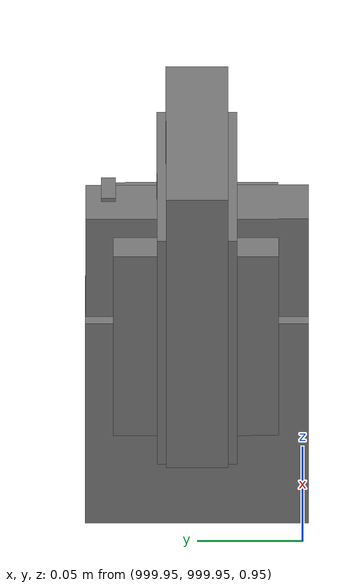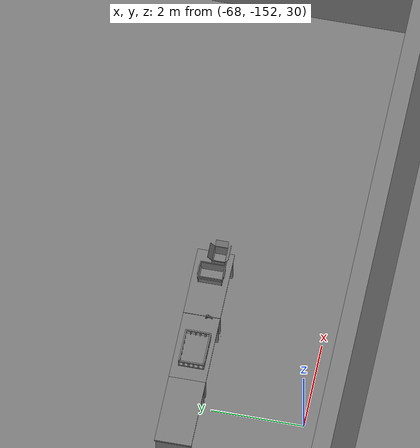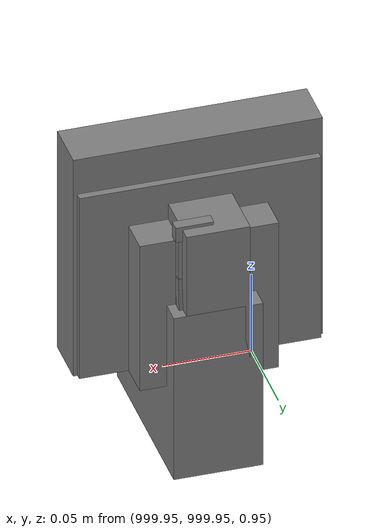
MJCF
<mujoco>
    <option gravity="0.000000000 0.000000000 -9.810000420" timestep="0.0049999999" integrator="implicitfast" density="1.225" viscosity="1.8000001e-05" noslip_iterations="10" iterations="100" sdf_iterations="50">
        <flag multiccd="disable"/>
    </option>
    <size memory="1000M"/>
    <compiler coordinate="local"/>
    <worldbody>
        <light cutoff="30" pos="0 1 1" dir="0 -1 -2"/>
        <light cutoff="30" pos="0 -1 1" dir="0 1 -2"/>
        <body pos="-66.352890015 -149.536224365 31.167020798" euler="-15.830487251 -6.804262638 72.526763916" mocap="true" name="spotlight4_SpotLight"/>
        <body pos="1000.000000000 1000.000000000 1.000000000" euler="0.000000000 0.000000000 180.000000000" name="openloong_gripper_2f85_fix_base_usda_battery_01">
            <geom contype="1" conaffinity="1" density="1000" type="box" material="" rgba="0.500000000 0.500000000 0.500000000 1.000000000" solimp="0.899999976 0.949999988 0.001000000" friction="1.000000000 0.005000000 0.000100000" solref="0.020000000 1.000000000" margin="0" condim="3" group="0" pos="-0.011123657 -0.041940309 0.101691343" quat="1.000000000 0.000000000 0.000000000 0.000000000" size="0.010800000 0.003375000 0.004725000" name="openloong_gripper_2f85_fix_base_usda_geom_1D77751E_9050_42DE_950F_B11F54B1F7F1"/>
            <geom contype="1" conaffinity="1" density="1000" type="box" material="" rgba="0.500000000 0.500000000 0.500000000 1.000000000" solimp="0.899999976 0.949999988 0.001000000" friction="1.000000000 0.005000000 0.000100000" solref="0.020000000 1.000000000" margin="0" condim="3" group="0" pos="-0.010876465 -0.044247437 0.047066893" quat="0.998702705 -0.050920475 0.000000000 0.000000000" size="0.009450001 0.002700000 0.024975000" name="openloong_gripper_2f85_fix_base_usda_geom_34229589_D5C0_4C1A_8568_C433B1B8303C"/>
            <geom contype="1" conaffinity="1" density="1000" type="box" material="" rgba="0.500000000 0.500000000 0.500000000 1.000000000" solimp="0.899999976 0.949999988 0.001000000" friction="1.000000000 0.005000000 0.000100000" solref="0.020000000 1.000000000" margin="0" condim="3" group="0" pos="-0.001235962 -0.000659180 0.047381196" quat="1.000000000 0.000000000 0.000000000 0.000000000" size="0.039420001 0.039150000 0.047250003" name="openloong_gripper_2f85_fix_base_usda_geom_2C3C6FD8_7BB4_45E8_908E_1AD3A774E180"/>
            <geom contype="1" conaffinity="1" density="1000" type="box" material="" rgba="0.500000000 0.500000000 0.500000000 1.000000000" solimp="0.899999976 0.949999988 0.001000000" friction="1.000000000 0.005000000 0.000100000" solref="0.020000000 1.000000000" margin="0" condim="3" group="0" pos="-0.010876465 -0.039138794 0.009851727" quat="1.000000000 0.000000000 0.000000000 0.000000000" size="0.009450001 0.010800000 0.013500000" name="openloong_gripper_2f85_fix_base_usda_geom_402CACE6_DDF4_4F15_A28E_D602BFBF61B3"/>
            <geom contype="1" conaffinity="1" density="1000" type="box" material="" rgba="0.500000000 0.500000000 0.500000000 1.000000000" solimp="0.899999976 0.949999988 0.001000000" friction="1.000000000 0.005000000 0.000100000" solref="0.020000000 1.000000000" margin="0" condim="3" group="0" pos="-0.010876465 -0.041528322 0.071508206" quat="1.000000000 0.000000000 0.000000000 0.000000000" size="0.009450001 0.002700000 0.027000001" name="openloong_gripper_2f85_fix_base_usda_geom_1CCE69C0_5556_4CA5_A6C7_4DEE17BA0A98"/>
            <freejoint name="openloong_gripper_2f85_fix_base_usda_battery_01_joint"/>
            <site size="0.005000000 0.005000000 0.005000000" rgba="0.500000000 0.500000000 0.500000000 1.000000000" pos="0.000000000 0.000000000 0.000000000" quat="0.999961913 0.008726500 0.000000000 0.000000000" group="0" type="sphere" name="openloong_gripper_2f85_fix_base_usda_battery_01site"/>
        </body>
        <body pos="-65.922248840 -149.678161621 31.168539047" euler="39.910453796 -27.312887192 52.868148804" mocap="true" name="spotlight3_SpotLight"/>
        <body pos="1000.000000000 1000.000000000 1.000000000" euler="0.000000000 0.000000000 180.000000000" name="openloong_gripper_2f85_fix_base_usda_cpu_fan">
            <geom contype="1" conaffinity="1" density="1000" type="box" material="" rgba="0.500000000 0.500000000 0.500000000 1.000000000" solimp="0.899999976 0.949999988 0.001000000" friction="1.000000000 0.005000000 0.000100000" solref="0.020000000 1.000000000" margin="0" condim="3" group="0" pos="0.000000000 0.000000000 0.070034981" quat="0.000000000 0.000000000 0.000000000 1.000000000" size="0.070700005 0.014699999 0.070700005" name="openloong_gripper_2f85_fix_base_usda_geom_5AA95A0A_8F2E_4A8E_8759_5C44FCB0DF46"/>
            <freejoint name="openloong_gripper_2f85_fix_base_usda_cpu_fan_joint"/>
            <site size="0.005000000 0.005000000 0.005000000" rgba="0.500000000 0.500000000 0.500000000 1.000000000" pos="0.000000000 0.000000000 0.000000000" quat="0.999961913 0.008726535 0.000000000 0.000000000" group="0" type="sphere" name="openloong_gripper_2f85_fix_base_usda_cpu_fancsite"/>
        </body>
        <body pos="1000.000000000 1000.000000000 1.000000000" euler="0.000000000 0.000000000 180.000000000" name="openloong_gripper_2f85_fix_base_usda_wifi_box">
            <geom contype="1" conaffinity="1" density="1000" type="box" material="" rgba="0.500000000 0.500000000 0.500000000 1.000000000" solimp="0.899999976 0.949999988 0.001000000" friction="1.000000000 0.005000000 0.000100000" solref="0.020000000 1.000000000" margin="0" condim="3" group="0" pos="0.000000000 0.000000000 0.058978677" quat="0.000000000 0.000000047 0.000000000 1.000000000" size="0.068499997 0.018999999 0.059000000" name="openloong_gripper_2f85_fix_base_usda_geom_CA3BC777_E252_4C32_A27B_08A7273CD934"/>
            <freejoint name="openloong_gripper_2f85_fix_base_usda_wifi_box_joint"/>
            <site size="0.005000000 0.005000000 0.005000000" rgba="0.500000000 0.500000000 0.500000000 1.000000000" pos="0.000000000 0.000000000 0.000000000" quat="0.999961913 0.008726500 0.000000000 0.000000000" group="0" type="sphere" name="openloong_gripper_2f85_fix_base_usda_wifi_boxsite"/>
        </body>
        <body pos="1000.000000000 1000.000000000 1.000000000" euler="0.000011953 0.000005123 -179.999984741" name="openloong_gripper_2f85_fix_base_usda_intel_box">
            <geom contype="1" conaffinity="1" density="1000" type="box" material="" rgba="0.500000000 0.500000000 0.500000000 1.000000000" solimp="0.899999976 0.949999988 0.001000000" friction="1.000000000 0.005000000 0.000100000" solref="0.020000000 1.000000000" margin="0" condim="3" group="0" pos="0.000000000 -0.000067139 0.000082284" quat="0.707106709 0.000000225 0.000000253 0.707106650" size="0.052800003 0.025300000 0.052800003" name="openloong_gripper_2f85_fix_base_usda_geom_A2C8065F_145E_4645_A7B2_522687DF06C5"/>
            <freejoint name="openloong_gripper_2f85_fix_base_usda_intel_box_joint"/>
            <site size="0.005000000 0.005000000 0.005000000" rgba="0.500000000 0.500000000 0.500000000 1.000000000" pos="0.000000000 0.000000000 0.000000000" quat="0.999961913 0.008726500 0.000000000 0.000000000" group="0" type="sphere" name="openloong_gripper_2f85_fix_base_usda_intel_boxsite"/>
        </body>
        <body pos="1000.000000000 999.999938965 1.000000000" euler="0.000000000 0.000000000 180.000000000" name="openloong_gripper_2f85_fix_base_usda_intelcore_i5">
            <geom contype="1" conaffinity="1" density="1000" type="box" material="" rgba="0.500000000 0.500000000 0.500000000 1.000000000" solimp="0.899999976 0.949999988 0.001000000" friction="1.000000000 0.005000000 0.000100000" solref="0.020000000 1.000000000" margin="0" condim="3" group="0" pos="0.000000000 0.000000000 0.051722717" quat="0.707106709 0.000000000 0.000000000 -0.707106769" size="0.052800000 0.018080002 0.052800000" name="openloong_gripper_2f85_fix_base_usda_geom_B5FB6F9D_CC6E_4F17_8E70_2659D0438E7B"/>
            <freejoint name="openloong_gripper_2f85_fix_base_usda_intelcore_i5_joint"/>
            <site size="0.005000000 0.005000000 0.005000000" rgba="0.500000000 0.500000000 0.500000000 1.000000000" pos="0.000000000 0.000000000 0.000000000" quat="0.999961913 0.008726534 0.000000000 0.000000000" group="0" type="sphere" name="openloong_gripper_2f85_fix_base_usda_intelcore_i5site"/>
        </body>
        <body pos="-65.940338135 -149.412078857 31.171443939" euler="132.059020996 -71.019470215 -15.255180359" mocap="true" name="spotlight2_SpotLight"/>
        <body pos="-64.866622925 -149.383972168 30.183746338" euler="89.999984741 89.999946594 0.000000000" name="openloong_gripper_2f85_fix_base_usda_bluebox_01">
            <geom contype="1" conaffinity="1" density="1000" type="box" material="" rgba="0.500000000 0.500000000 0.500000000 1.000000000" solimp="0.899999976 0.949999988 0.001000000" friction="1.000000000 0.005000000 0.000100000" solref="0.020000000 1.000000000" margin="0" condim="3" group="0" pos="0.276580811 0.187225342 0.000068665" quat="0.707106948 0.000077471 0.707106352 0.000077486" size="0.100000001 0.057999998 0.010000000" name="openloong_gripper_2f85_fix_base_usda_geom_77075A82_405B_40A7_A228_8E4A9B39CC65"/>
            <geom contype="1" conaffinity="1" density="1000" type="box" material="" rgba="0.500000000 0.500000000 0.500000000 1.000000000" solimp="0.899999976 0.949999988 0.001000000" friction="1.000000000 0.005000000 0.000100000" solref="0.020000000 1.000000000" margin="0" condim="3" group="0" pos="0.000000000 0.002883911 0.000000000" quat="0.999999881 0.000000000 0.000000000 0.000000000" size="0.254000008 0.003000000 0.172000006" name="openloong_gripper_2f85_fix_base_usda_geom_529B8E9D_1679_486A_AA99_F3B6976BAB28"/>
            <geom contype="1" conaffinity="1" density="1000" type="box" material="" rgba="0.500000000 0.500000000 0.500000000 1.000000000" solimp="0.899999976 0.949999988 0.001000000" friction="1.000000000 0.005000000 0.000100000" solref="0.020000000 1.000000000" margin="0" condim="3" group="0" pos="0.000000000 0.124874115 0.173484802" quat="0.999796331 0.020176515 -0.000000015 0.000000030" size="0.259999990 0.119999997 0.007000000" name="openloong_gripper_2f85_fix_base_usda_geom_259E4B1E_86F5_472A_87F8_AE927486BA13"/>
            <geom contype="1" conaffinity="1" density="1000" type="box" material="" rgba="0.500000000 0.500000000 0.500000000 1.000000000" solimp="0.899999976 0.949999988 0.001000000" friction="1.000000000 0.005000000 0.000100000" solref="0.020000000 1.000000000" margin="0" condim="3" group="0" pos="0.000000000 0.124874115 -0.173469543" quat="0.999796331 -0.020176545 -0.000000015 0.000000000" size="0.259999990 0.119999997 0.007000000" name="openloong_gripper_2f85_fix_base_usda_geom_6CD254DE_574C_476D_B456_BFECD55127EA"/>
            <geom contype="1" conaffinity="1" density="1000" type="box" material="" rgba="0.500000000 0.500000000 0.500000000 1.000000000" solimp="0.899999976 0.949999988 0.001000000" friction="1.000000000 0.005000000 0.000100000" solref="0.020000000 1.000000000" margin="0" condim="3" group="0" pos="0.000000000 0.214008331 0.188980103" quat="0.999912977 0.013176724 0.000000015 0.000000000" size="0.259999990 0.029999999 0.012500000" name="openloong_gripper_2f85_fix_base_usda_geom_F6D70A8B_4EBE_49F1_8042_DF3A3EA011B1"/>
            <geom contype="1" conaffinity="1" density="1000" type="box" material="" rgba="0.500000000 0.500000000 0.500000000 1.000000000" solimp="0.899999976 0.949999988 0.001000000" friction="1.000000000 0.005000000 0.000100000" solref="0.020000000 1.000000000" margin="0" condim="3" group="0" pos="-0.258361816 0.125289917 0.001876831" quat="0.702796936 -0.020792112 0.710783124 0.020769298" size="0.189999998 0.119999997 0.009000000" name="openloong_gripper_2f85_fix_base_usda_geom_B28BF017_4371_4C55_A7BB_5ACD4482F601"/>
            <geom contype="1" conaffinity="1" density="1000" type="box" material="" rgba="0.500000000 0.500000000 0.500000000 1.000000000" solimp="0.899999976 0.949999988 0.001000000" friction="1.000000000 0.005000000 0.000100000" solref="0.020000000 1.000000000" margin="0" condim="3" group="0" pos="0.000000000 0.214008331 -0.188980103" quat="0.999912977 -0.013176769 0.000000030 0.000000015" size="0.259999990 0.029999999 0.012500000" name="openloong_gripper_2f85_fix_base_usda_geom_36173BCE_7A36_4089_A88C_E23DBBBAB07E"/>
            <geom contype="1" conaffinity="1" density="1000" type="box" material="" rgba="0.500000000 0.500000000 0.500000000 1.000000000" solimp="0.899999976 0.949999988 0.001000000" friction="1.000000000 0.005000000 0.000100000" solref="0.020000000 1.000000000" margin="0" condim="3" group="0" pos="-0.276611328 0.187225342 0.000068665" quat="0.707106650 0.000077441 0.707106709 0.000077456" size="0.100000001 0.057999998 0.010000000" name="openloong_gripper_2f85_fix_base_usda_geom_F3C0A018_F1CF_4411_A85D_8A3B69F1F658"/>
            <geom contype="1" conaffinity="1" density="1000" type="box" material="" rgba="0.500000000 0.500000000 0.500000000 1.000000000" solimp="0.899999976 0.949999988 0.001000000" friction="1.000000000 0.005000000 0.000100000" solref="0.020000000 1.000000000" margin="0" condim="3" group="0" pos="0.258331299 0.125289917 0.001876831" quat="0.702851415 0.018856421 0.710823774 -0.019329369" size="0.189999998 0.119999997 0.009000000" name="openloong_gripper_2f85_fix_base_usda_geom_DBAB2557_FA17_4414_A016_702E1895D2C4"/>
            <freejoint name="openloong_gripper_2f85_fix_base_usda_bluebox_01_joint"/>
            <site size="0.005000000 0.005000000 0.005000000" rgba="0.500000000 0.500000000 0.500000000 1.000000000" pos="0.000000000 0.000000000 0.000000000" quat="0.999961913 0.008726534 0.000000000 0.000000000" group="0" type="sphere" name="openloong_gripper_2f85_fix_base_usda_bluebox_01site"/>
        </body>
        <body pos="-64.496299744 -149.491867065 30.235729218" euler="0.000000000 0.000000000 89.999946594" name="openloong_gripper_2f85_fix_base_usda_cardboardbox_01">
            <geom contype="1" conaffinity="1" density="1000" type="box" material="" rgba="0.500000000 0.500000000 0.500000000 1.000000000" solimp="0.899999976 0.949999988 0.001000000" friction="1.000000000 0.005000000 0.000100000" solref="0.020000000 1.000000000" margin="0" condim="3" group="0" pos="-0.003166199 -0.004086494 0.005052090" quat="1.000000000 0.000000000 0.000000000 0.000000000" size="0.142499998 0.177500010 0.005000000" name="openloong_gripper_2f85_fix_base_usda_geom_E4D04A24_8814_4A56_BCEA_AE8DA6EA8882"/>
            <geom contype="1" conaffinity="1" density="1000" type="box" material="" rgba="0.500000000 0.500000000 0.500000000 1.000000000" solimp="0.899999976 0.949999988 0.001000000" friction="1.000000000 0.005000000 0.000100000" solref="0.020000000 1.000000000" margin="0" condim="3" group="0" pos="-0.003166199 0.170316696 0.150570869" quat="1.000000000 0.000000000 0.000000000 0.000000000" size="0.142499998 0.005000000 0.149999991" name="openloong_gripper_2f85_fix_base_usda_geom_BF562F92_B05A_4BAC_A9C4_471B01325833"/>
            <geom contype="1" conaffinity="1" density="1000" type="box" material="" rgba="0.500000000 0.500000000 0.500000000 1.000000000" solimp="0.899999976 0.949999988 0.001000000" friction="1.000000000 0.005000000 0.000100000" solref="0.020000000 1.000000000" margin="0" condim="3" group="0" pos="-0.147399902 -0.005307198 0.150570869" quat="1.000000000 0.000000000 0.000000000 0.000000000" size="0.005000000 0.177500010 0.149999991" name="openloong_gripper_2f85_fix_base_usda_geom_D0F05C42_EE39_4E7C_B57C_A9ADB8530BB2"/>
            <geom contype="1" conaffinity="1" density="1000" type="box" material="" rgba="0.500000000 0.500000000 0.500000000 1.000000000" solimp="0.899999976 0.949999988 0.001000000" friction="1.000000000 0.005000000 0.000100000" solref="0.020000000 1.000000000" margin="0" condim="3" group="0" pos="0.140275955 -0.005307198 0.150570869" quat="1.000000000 0.000000000 0.000000000 0.000000000" size="0.005000000 0.177500010 0.149999991" name="openloong_gripper_2f85_fix_base_usda_geom_DDEFCB79_C8FB_4F3B_BCD0_CA2757E836A7"/>
            <geom contype="1" conaffinity="1" density="1000" type="box" material="" rgba="0.500000000 0.500000000 0.500000000 1.000000000" solimp="0.899999976 0.949999988 0.001000000" friction="1.000000000 0.005000000 0.000100000" solref="0.020000000 1.000000000" margin="0" condim="3" group="0" pos="-0.003166199 -0.181550980 0.150570869" quat="1.000000000 0.000000000 0.000000000 0.000000000" size="0.142499998 0.005000000 0.149999991" name="openloong_gripper_2f85_fix_base_usda_geom_400B6894_6FA4_4D59_A9C1_F1E1541FB5D9"/>
            <freejoint name="openloong_gripper_2f85_fix_base_usda_cardboardbox_01_joint"/>
            <site size="0.005000000 0.005000000 0.005000000" rgba="0.500000000 0.500000000 0.500000000 1.000000000" pos="0.000000000 0.000000000 0.000000000" quat="0.999961913 0.008726535 0.000000000 0.000000000" group="0" type="sphere" name="openloong_gripper_2f85_fix_base_usda_site_05596815_6ACD_445C_B944_3D5FA402EDE7"/>
            <body pos="0.139160156 -0.004048347 0.301930904" euler="-179.999954224 49.383502960 179.999954224" name="openloong_gripper_2f85_fix_base_usda_A1_006">
                <geom contype="1" conaffinity="1" density="1000" type="box" material="" rgba="0.500000000 0.500000000 0.500000000 1.000000000" solimp="0.899999976 0.949999988 0.001000000" friction="1.000000000 0.005000000 0.000100000" solref="0.020000000 1.000000000" margin="0" condim="3" group="0" pos="-0.071587563 0.000009537 0.001745224" quat="0.999999881 0.000000000 0.000000000 0.000000000" size="0.071249999 0.179999992 0.002500000" name="openloong_gripper_2f85_fix_base_usda_geom_B325F425_400D_406D_B93B_499478B4AB6F"/>
                <joint armature="0" stiffness="0.07" damping="0.0099999998" axis="0.000000 1.000000 0.000000" type="hinge" name="openloong_gripper_2f85_fix_base_usda_A1_006"/>
            </body>
            <body pos="-0.145902634 -0.004086494 0.301938057" euler="-180.000000000 -60.000011444 -180.000000000" name="openloong_gripper_2f85_fix_base_usda_A2_006">
                <geom contype="1" conaffinity="1" density="1000" type="box" material="" rgba="0.500000000 0.500000000 0.500000000 1.000000000" solimp="0.899999976 0.949999988 0.001000000" friction="1.000000000 0.005000000 0.000100000" solref="0.020000000 1.000000000" margin="0" condim="3" group="0" pos="0.071268082 0.000009537 0.002717972" quat="0.000002921 0.000000000 -0.000000030 0.999999881" size="0.071249999 0.179999992 0.002500000" name="openloong_gripper_2f85_fix_base_usda_geom_45F757E0_A8D9_433E_BF18_F77C7B2FFB84"/>
                <joint armature="0" stiffness="0.07" damping="0.0099999998" axis="0.000000 1.000000 0.000000" type="hinge" name="openloong_gripper_2f85_fix_base_usda_A2_006"/>
            </body>
            <body pos="-0.003385544 0.175991058 0.301930904" euler="-125.858116150 -0.000004561 0.000002331" name="openloong_gripper_2f85_fix_base_usda_B2_006">
                <geom contype="1" conaffinity="1" density="1000" type="box" material="" rgba="0.500000000 0.500000000 0.500000000 1.000000000" solimp="0.899999976 0.949999988 0.001000000" friction="1.000000000 0.005000000 0.000100000" solref="0.020000000 1.000000000" margin="0" condim="3" group="0" pos="0.000009537 -0.070939064 -0.002470016" quat="0.999614120 0.027776197 -0.000000015 0.000000030" size="0.137500003 0.064999998 0.005000000" name="openloong_gripper_2f85_fix_base_usda_geom_89D1106B_4FEF_419F_ACA5_DAD68625EA2B"/>
                <joint armature="0" stiffness="0.07" damping="0.0099999998" axis="1.000000 0.000000 0.000000" type="hinge" name="openloong_gripper_2f85_fix_base_usda_B2_006"/>
            </body>
            <body pos="-0.003385544 -0.184140205 0.301938057" euler="147.805557251 0.000000000 0.000000000" name="openloong_gripper_2f85_fix_base_usda_B1_006">
                <geom contype="1" conaffinity="1" density="1000" type="box" material="" rgba="0.500000000 0.500000000 0.500000000 1.000000000" solimp="0.899999976 0.949999988 0.001000000" friction="1.000000000 0.005000000 0.000100000" solref="0.020000000 1.000000000" margin="0" condim="3" group="0" pos="-0.000028610 0.070202351 -0.002703667" quat="0.999614179 -0.027776167 0.000000000 0.000000000" size="0.137500003 0.064999998 0.005000000" name="openloong_gripper_2f85_fix_base_usda_geom_67EB083C_7A86_4945_829F_D834C3EBCF1F"/>
                <joint armature="0" stiffness="0.07" damping="0.0099999998" axis="1.000000 0.000000 0.000000" type="hinge" name="openloong_gripper_2f85_fix_base_usda_B1_006"/>
            </body>
        </body>
        <body pos="-65.882858276 -149.481979370 30.229999542" euler="-64.487716675 0.000000000 0.000000000" name="openloong_gripper_2f85_fix_base_usda_Barcode">
            <geom contype="1" conaffinity="1" density="1000" type="box" material="" rgba="0.500000000 0.500000000 0.500000000 1.000000000" solimp="0.899999976 0.949999988 0.001000000" friction="1.000000000 0.005000000 0.000100000" solref="0.020000000 1.000000000" margin="0" condim="3" group="0" pos="0.000000000 0.013038635 0.001419067" quat="0.000000000 0.000000000 0.000000000 1.000000119" size="0.034000002 0.010000000 0.017999999" name="openloong_gripper_2f85_fix_base_usda_geom_D8E9FED8_A16D_4A15_8591_B55522B0B3AA"/>
            <geom contype="1" conaffinity="1" density="1000" type="box" material="" rgba="0.500000000 0.500000000 0.500000000 1.000000000" solimp="0.899999976 0.949999988 0.001000000" friction="1.000000000 0.005000000 0.000100000" solref="0.020000000 1.000000000" margin="0" condim="3" group="0" pos="0.000000000 -0.035301208 -0.007095337" quat="0.000000000 0.000000000 -0.043619365 0.999048233" size="0.028999999 0.010000000 0.020000000" name="openloong_gripper_2f85_fix_base_usda_geom_5B096A2D_E945_4C87_983B_A3D3FC756E36"/>
            <geom contype="1" conaffinity="1" density="1000" type="box" material="" rgba="0.500000000 0.500000000 0.500000000 1.000000000" solimp="0.899999976 0.949999988 0.001000000" friction="1.000000000 0.005000000 0.000100000" solref="0.020000000 1.000000000" margin="0" condim="3" group="0" pos="0.000000000 -0.043411255 -0.011749268" quat="0.922262907 0.386563420 0.000000000 0.000000000" size="0.026000001 0.010000000 0.020000000" name="openloong_gripper_2f85_fix_base_usda_geom_232A7F2A_1748_4A03_B06B_51B724B320A1"/>
            <geom contype="1" conaffinity="1" density="1000" type="box" material="" rgba="0.500000000 0.500000000 0.500000000 1.000000000" solimp="0.899999976 0.949999988 0.001000000" friction="1.000000000 0.005000000 0.000100000" solref="0.020000000 1.000000000" margin="0" condim="3" group="0" pos="0.000000000 -0.016967773 -0.031860352" quat="0.000000000 0.000000000 0.000000000 1.000000119" size="0.008000000 0.010000000 0.013000000" name="openloong_gripper_2f85_fix_base_usda_geom_F16AC26F_C2CC_4F46_A6B2_2F7D44C68C7C"/>
            <geom contype="1" conaffinity="1" density="1000" type="box" material="" rgba="0.500000000 0.500000000 0.500000000 1.000000000" solimp="0.899999976 0.949999988 0.001000000" friction="1.000000000 0.005000000 0.000100000" solref="0.020000000 1.000000000" margin="0" condim="3" group="0" pos="0.000000000 -0.001869202 0.000312805" quat="0.953716993 0.300705761 0.000000000 0.000000000" size="0.032000002 0.010000000 0.018999999" name="openloong_gripper_2f85_fix_base_usda_geom_EFD59497_0087_436C_A990_080E5DCB4DE3"/>
            <geom contype="1" conaffinity="1" density="1000" type="box" material="" rgba="0.500000000 0.500000000 0.500000000 1.000000000" solimp="0.899999976 0.949999988 0.001000000" friction="1.000000000 0.005000000 0.000100000" solref="0.020000000 1.000000000" margin="0" condim="3" group="0" pos="0.000000000 -0.019531250 -0.003173828" quat="0.953716993 0.300705761 0.000000000 0.000000000" size="0.030999999 0.010000000 0.020000000" name="openloong_gripper_2f85_fix_base_usda_geom_70207A44_E61D_41BF_AB6D_8C0ADFC75555"/>
            <geom contype="1" conaffinity="1" density="1000" type="box" material="" rgba="0.500000000 0.500000000 0.500000000 1.000000000" solimp="0.899999976 0.949999988 0.001000000" friction="1.000000000 0.005000000 0.000100000" solref="0.020000000 1.000000000" margin="0" condim="3" group="0" pos="0.000000000 -0.035301208 -0.007095337" quat="0.953716993 0.300705761 0.000000000 0.000000000" size="0.028999999 0.010000000 0.020000000" name="openloong_gripper_2f85_fix_base_usda_geom_3DE5C7C2_BD1F_42A9_BD7E_3394AB071018"/>
            <geom contype="1" conaffinity="1" density="1000" type="box" material="" rgba="0.500000000 0.500000000 0.500000000 1.000000000" solimp="0.899999976 0.949999988 0.001000000" friction="1.000000000 0.005000000 0.000100000" solref="0.020000000 1.000000000" margin="0" condim="3" group="0" pos="0.000000000 -0.042617798 -0.071121216" quat="0.000000000 0.000000000 0.000000000 1.000000119" size="0.013000000 0.021000000 0.059999999" name="openloong_gripper_2f85_fix_base_usda_geom_A57635E2_37B3_4077_BD44_4106666CD863"/>
            <freejoint name="openloong_gripper_2f85_fix_base_usda_Barcode_joint"/>
            <site size="0.005000000 0.005000000 0.005000000" rgba="0.500000000 0.500000000 0.500000000 1.000000000" pos="0.000000000 0.000000000 0.000000000" quat="1.000000000 0.000000000 0.000000000 0.000000000" group="0" type="sphere" name="openloong_gripper_2f85_fix_base_usda_Barcode_site"/>
        </body>
        <body pos="-66.745018005 -149.392349243 30.184000015" euler="0.000000000 0.000000000 89.999946594" name="[22332231350635]_Basket_01">
            <geom contype="1" conaffinity="1" density="1000" type="box" material="" rgba="0.500000000 0.500000000 0.500000000 1.000000000" solimp="0.899999976 0.949999988 0.001000000" friction="1.000000000 0.005000000 0.000100000" solref="0.020000000 1.000000000" margin="0" condim="3" group="0" pos="-0.052425385 0.389207840 0.089787483" quat="0.707107008 0.000000000 0.000000000 0.707106411" size="0.014249999 0.014249999 0.059999999" name="[22332231350635]_geom_51A08A47_9C7C_4E4C_90B3_E19984B547EB"/>
            <geom contype="1" conaffinity="1" density="1000" type="box" material="" rgba="0.500000000 0.500000000 0.500000000 1.000000000" solimp="0.899999976 0.949999988 0.001000000" friction="1.000000000 0.005000000 0.000100000" solref="0.020000000 1.000000000" margin="0" condim="3" group="0" pos="0.264015198 -0.133043289 0.089787483" quat="0.707107008 0.000000000 0.000000000 0.707106411" size="0.014249999 0.014249999 0.059999999" name="[22332231350635]_geom_D956BA20_7382_4B4B_9EA0_37B0FD0EFC48"/>
            <geom contype="1" conaffinity="1" density="1000" type="box" material="" rgba="0.500000000 0.500000000 0.500000000 1.000000000" solimp="0.899999976 0.949999988 0.001000000" friction="1.000000000 0.005000000 0.000100000" solref="0.020000000 1.000000000" margin="0" condim="3" group="0" pos="-0.264015198 -0.265548706 0.089793205" quat="0.707107008 0.000000000 0.000000000 0.707106411" size="0.014249999 0.014249999 0.059999999" name="[22332231350635]_geom_1F2DD6EC_6E1F_444D_8B94_1C2DAC176421"/>
            <geom contype="1" conaffinity="1" density="1000" type="box" material="" rgba="0.500000000 0.500000000 0.500000000 1.000000000" solimp="0.899999976 0.949999988 0.001000000" friction="1.000000000 0.005000000 0.000100000" solref="0.020000000 1.000000000" margin="0" condim="3" group="0" pos="-0.160263062 -0.389322281 0.089793205" quat="0.707107008 0.000000000 0.000000000 0.707106411" size="0.014249999 0.014249999 0.059999999" name="[22332231350635]_geom_8A54D917_9EE6_4E3A_A9C2_A47B976065EA"/>
            <geom contype="1" conaffinity="1" density="1000" type="box" material="" rgba="0.500000000 0.500000000 0.500000000 1.000000000" solimp="0.899999976 0.949999988 0.001000000" friction="1.000000000 0.005000000 0.000100000" solref="0.020000000 1.000000000" margin="0" condim="3" group="0" pos="0.162265778 -0.389322281 0.089787483" quat="0.707107008 0.000000000 0.000000000 0.707106411" size="0.014249999 0.014249999 0.059999999" name="[22332231350635]_geom_970EC47F_0CD2_41FD_A271_952B9A3011ED"/>
            <geom contype="1" conaffinity="1" density="1000" type="box" material="" rgba="0.500000000 0.500000000 0.500000000 1.000000000" solimp="0.899999976 0.949999988 0.001000000" friction="1.000000000 0.005000000 0.000100000" solref="0.020000000 1.000000000" margin="0" condim="3" group="0" pos="0.264015198 0.389207840 0.089787483" quat="0.707107008 0.000000000 0.000000000 0.707106411" size="0.014249999 0.014249999 0.059999999" name="[22332231350635]_geom_32159228_489A_4D8E_B1B4_ECE1D73B61F8"/>
            <geom contype="1" conaffinity="1" density="1000" type="box" material="" rgba="0.500000000 0.500000000 0.500000000 1.000000000" solimp="0.899999976 0.949999988 0.001000000" friction="1.000000000 0.005000000 0.000100000" solref="0.020000000 1.000000000" margin="0" condim="3" group="0" pos="-0.264015198 -0.133043289 0.089793205" quat="0.707107008 0.000000000 0.000000000 0.707106411" size="0.014249999 0.014249999 0.059999999" name="[22332231350635]_geom_E2097B2C_607D_4450_ACBE_30A5787A73EA"/>
            <geom contype="1" conaffinity="1" density="1000" type="box" material="" rgba="0.500000000 0.500000000 0.500000000 1.000000000" solimp="0.899999976 0.949999988 0.001000000" friction="1.000000000 0.005000000 0.000100000" solref="0.020000000 1.000000000" margin="0" condim="3" group="0" pos="-0.264026642 0.269256592 0.089793205" quat="0.707107008 0.000000000 0.000000000 0.707106411" size="0.014249999 0.014249999 0.059999999" name="[22332231350635]_geom_02C8460A_A739_4FD2_AD08_EB679736474E"/>
            <geom contype="1" conaffinity="1" density="1000" type="box" material="" rgba="0.500000000 0.500000000 0.500000000 1.000000000" solimp="0.899999976 0.949999988 0.001000000" friction="1.000000000 0.005000000 0.000100000" solref="0.020000000 1.000000000" margin="0" condim="3" group="0" pos="0.054462433 0.389207840 0.089787483" quat="0.707107008 0.000000000 0.000000000 0.707106411" size="0.014249999 0.014249999 0.059999999" name="[22332231350635]_geom_E9A2852B_2594_4789_9A69_04C88EA3FBCB"/>
            <geom contype="1" conaffinity="1" density="1000" type="box" material="" rgba="0.500000000 0.500000000 0.500000000 1.000000000" solimp="0.899999976 0.949999988 0.001000000" friction="1.000000000 0.005000000 0.000100000" solref="0.020000000 1.000000000" margin="0" condim="3" group="0" pos="0.054462433 -0.389322281 0.089787483" quat="0.707107008 0.000000000 0.000000000 0.707106411" size="0.014249999 0.014249999 0.059999999" name="[22332231350635]_geom_59F590FF_2095_48D4_A805_BAE61BF58525"/>
            <geom contype="1" conaffinity="1" density="1000" type="box" material="" rgba="0.500000000 0.500000000 0.500000000 1.000000000" solimp="0.899999976 0.949999988 0.001000000" friction="1.000000000 0.005000000 0.000100000" solref="0.020000000 1.000000000" margin="0" condim="3" group="0" pos="0.264015198 0.269256592 0.089793205" quat="0.707107008 0.000000000 0.000000000 0.707106411" size="0.014249999 0.014249999 0.059999999" name="[22332231350635]_geom_26DA89A6_4730_4BB2_96BA_21D6C616B19E"/>
            <geom contype="1" conaffinity="1" density="1000" type="box" material="" rgba="0.500000000 0.500000000 0.500000000 1.000000000" solimp="0.899999976 0.949999988 0.001000000" friction="1.000000000 0.005000000 0.000100000" solref="0.020000000 1.000000000" margin="0" condim="3" group="0" pos="0.264015198 -0.389322281 0.089787483" quat="0.707107008 0.000000000 0.000000000 0.707106411" size="0.014249999 0.014249999 0.059999999" name="[22332231350635]_geom_4D85655A_39BB_4675_AB94_B3B0A3FC3FC1"/>
            <geom contype="1" conaffinity="1" density="1000" type="box" material="" rgba="0.500000000 0.500000000 0.500000000 1.000000000" solimp="0.899999976 0.949999988 0.001000000" friction="1.000000000 0.005000000 0.000100000" solref="0.020000000 1.000000000" margin="0" condim="3" group="0" pos="0.000000000 0.000000000 0.015998840" quat="0.707107008 0.000000000 0.000000000 0.707106411" size="0.403499991 0.279000014 0.015750000" name="[22332231350635]_geom_AD47A219_B0C9_4123_96A8_DC23061D2600"/>
            <geom contype="1" conaffinity="1" density="1000" type="box" material="" rgba="0.500000000 0.500000000 0.500000000 1.000000000" solimp="0.899999976 0.949999988 0.001000000" friction="1.000000000 0.005000000 0.000100000" solref="0.020000000 1.000000000" margin="0" condim="3" group="0" pos="0.000000000 -0.389476776 0.163619041" quat="0.707107008 0.000000000 0.000000000 0.707106411" size="0.015000000 0.277500004 0.015750000" name="[22332231350635]_geom_DA8F7A2F_7C1E_4AB4_9DBF_D3C9CC7F49BE"/>
            <geom contype="1" conaffinity="1" density="1000" type="box" material="" rgba="0.500000000 0.500000000 0.500000000 1.000000000" solimp="0.899999976 0.949999988 0.001000000" friction="1.000000000 0.005000000 0.000100000" solref="0.020000000 1.000000000" margin="0" condim="3" group="0" pos="0.162265778 0.389207840 0.089787483" quat="0.707107008 0.000000000 0.000000000 0.707106411" size="0.014249999 0.014249999 0.059999999" name="[22332231350635]_geom_53FE0D60_70AB_4123_A364_5A4959BC2880"/>
            <geom contype="1" conaffinity="1" density="1000" type="box" material="" rgba="0.500000000 0.500000000 0.500000000 1.000000000" solimp="0.899999976 0.949999988 0.001000000" friction="1.000000000 0.005000000 0.000100000" solref="0.020000000 1.000000000" margin="0" condim="3" group="0" pos="0.000000000 0.389471054 0.163619041" quat="0.707107008 0.000000000 0.000000000 0.707106411" size="0.015000000 0.277500004 0.015750000" name="[22332231350635]_geom_2284C655_0952_4AE3_B70C_37BA656BD52E"/>
            <geom contype="1" conaffinity="1" density="1000" type="box" material="" rgba="0.500000000 0.500000000 0.500000000 1.000000000" solimp="0.899999976 0.949999988 0.001000000" friction="1.000000000 0.005000000 0.000100000" solref="0.020000000 1.000000000" margin="0" condim="3" group="0" pos="-0.263511658 0.000000000 0.163619041" quat="0.707107008 0.000000000 0.000000000 0.707106411" size="0.403499991 0.015000000 0.015750000" name="[22332231350635]_geom_EF966CAD_31A2_425D_98A4_877C3B765614"/>
            <geom contype="1" conaffinity="1" density="1000" type="box" material="" rgba="0.500000000 0.500000000 0.500000000 1.000000000" solimp="0.899999976 0.949999988 0.001000000" friction="1.000000000 0.005000000 0.000100000" solref="0.020000000 1.000000000" margin="0" condim="3" group="0" pos="-0.264015198 0.141334534 0.089793205" quat="0.707107008 0.000000000 0.000000000 0.707106411" size="0.014249999 0.014249999 0.059999999" name="[22332231350635]_geom_244F71C0_8C1A_43A0_804D_B2562A572881"/>
            <geom contype="1" conaffinity="1" density="1000" type="box" material="" rgba="0.500000000 0.500000000 0.500000000 1.000000000" solimp="0.899999976 0.949999988 0.001000000" friction="1.000000000 0.005000000 0.000100000" solref="0.020000000 1.000000000" margin="0" condim="3" group="0" pos="0.264015198 -0.265548706 0.089787483" quat="0.707107008 0.000000000 0.000000000 0.707106411" size="0.014249999 0.014249999 0.059999999" name="[22332231350635]_geom_74CFE5FA_6CBD_4CDD_9AEA_79FBE5B5D568"/>
            <geom contype="1" conaffinity="1" density="1000" type="box" material="" rgba="0.500000000 0.500000000 0.500000000 1.000000000" solimp="0.899999976 0.949999988 0.001000000" friction="1.000000000 0.005000000 0.000100000" solref="0.020000000 1.000000000" margin="0" condim="3" group="0" pos="-0.160263062 0.389207840 0.089787483" quat="0.707107008 0.000000000 0.000000000 0.707106411" size="0.014249999 0.014249999 0.059999999" name="[22332231350635]_geom_64FEA75F_E9F6_40A8_BADC_B3EDAF27EC37"/>
            <geom contype="1" conaffinity="1" density="1000" type="box" material="" rgba="0.500000000 0.500000000 0.500000000 1.000000000" solimp="0.899999976 0.949999988 0.001000000" friction="1.000000000 0.005000000 0.000100000" solref="0.020000000 1.000000000" margin="0" condim="3" group="0" pos="-0.052425385 -0.389322281 0.089787483" quat="0.707107008 0.000000000 0.000000000 0.707106411" size="0.014249999 0.014249999 0.059999999" name="[22332231350635]_geom_E082775B_14E1_4292_871A_57B7186BC177"/>
            <geom contype="1" conaffinity="1" density="1000" type="box" material="" rgba="0.500000000 0.500000000 0.500000000 1.000000000" solimp="0.899999976 0.949999988 0.001000000" friction="1.000000000 0.005000000 0.000100000" solref="0.020000000 1.000000000" margin="0" condim="3" group="0" pos="-0.264026642 -0.389322281 0.089793205" quat="0.707107008 0.000000000 0.000000000 0.707106411" size="0.014249999 0.014249999 0.059999999" name="[22332231350635]_geom_EC7F8D5B_59FD_436B_B952_D182ECE0DC3F"/>
            <geom contype="1" conaffinity="1" density="1000" type="box" material="" rgba="0.500000000 0.500000000 0.500000000 1.000000000" solimp="0.899999976 0.949999988 0.001000000" friction="1.000000000 0.005000000 0.000100000" solref="0.020000000 1.000000000" margin="0" condim="3" group="0" pos="0.264015198 0.141334534 0.089787483" quat="0.707107008 0.000000000 0.000000000 0.707106411" size="0.014249999 0.014249999 0.059999999" name="[22332231350635]_geom_47F15E8F_062B_4590_9F91_741CC76D9247"/>
            <geom contype="1" conaffinity="1" density="1000" type="box" material="" rgba="0.500000000 0.500000000 0.500000000 1.000000000" solimp="0.899999976 0.949999988 0.001000000" friction="1.000000000 0.005000000 0.000100000" solref="0.020000000 1.000000000" margin="0" condim="3" group="0" pos="-0.264015198 0.389207840 0.089793205" quat="0.707107008 0.000000000 0.000000000 0.707106411" size="0.014249999 0.014249999 0.059999999" name="[22332231350635]_geom_4F4F64DE_FFE9_45E9_8C2F_E3F0AEF08C41"/>
            <geom contype="1" conaffinity="1" density="1000" type="box" material="" rgba="0.500000000 0.500000000 0.500000000 1.000000000" solimp="0.899999976 0.949999988 0.001000000" friction="1.000000000 0.005000000 0.000100000" solref="0.020000000 1.000000000" margin="0" condim="3" group="0" pos="0.264015198 0.004480362 0.089787483" quat="0.707107008 0.000000000 0.000000000 0.707106411" size="0.014249999 0.014249999 0.059999999" name="[22332231350635]_geom_2790284E_DC8C_461C_A135_49FDEC42AD35"/>
            <geom contype="1" conaffinity="1" density="1000" type="box" material="" rgba="0.500000000 0.500000000 0.500000000 1.000000000" solimp="0.899999976 0.949999988 0.001000000" friction="1.000000000 0.005000000 0.000100000" solref="0.020000000 1.000000000" margin="0" condim="3" group="0" pos="0.263694763 -0.000011444 0.163619041" quat="0.707107008 0.000000000 0.000000000 0.707106411" size="0.403499991 0.015000000 0.015750000" name="[22332231350635]_geom_AC23340A_A48B_408A_A8C1_C5F2B0F2DE9B"/>
            <geom contype="1" conaffinity="1" density="1000" type="box" material="" rgba="0.500000000 0.500000000 0.500000000 1.000000000" solimp="0.899999976 0.949999988 0.001000000" friction="1.000000000 0.005000000 0.000100000" solref="0.020000000 1.000000000" margin="0" condim="3" group="0" pos="-0.264015198 0.004480362 0.089793205" quat="0.707107008 0.000000000 0.000000000 0.707106411" size="0.014249999 0.014249999 0.059999999" name="[22332231350635]_geom_14440785_C987_4A63_A69A_A17FBAA3C8FD"/>
            <freejoint name="[22332231350635]_joint_4193A8E0_FFA9_451E_88C3_D9584B7B5228"/>
        </body>
        <body pos="0.000000000 0.000000000 0.000000000" euler="0.000000000 0.000000000 0.000000000" name="Static Objects_Static Objects">
            <geom contype="1" conaffinity="1" density="1000" type="box" material="" rgba="0.500000000 0.500000000 0.500000000 1.000000000" solimp="0.899999976 0.949999988 0.001000000" friction="1.000000000 0.005000000 0.000100000" solref="0.020000000 1.000000000" margin="0" condim="3" group="0" pos="-67.544113159 -149.365814209 29.727830887" quat="0.500000417 0.499999970 0.499999553 0.499999970" size="0.381000012 0.319999993 0.041000001" name="Static Objects_geom_6AE9935F_B43C_440C_8532_D4E50F13BF58"/>
            <geom contype="1" conaffinity="1" density="1000" type="box" material="" rgba="0.500000000 0.500000000 0.500000000 1.000000000" solimp="0.899999976 0.949999988 0.001000000" friction="1.000000000 0.005000000 0.000100000" solref="0.020000000 1.000000000" margin="0" condim="3" group="0" pos="-68.239501953 -149.365814209 30.086868286" quat="0.500000417 0.499999970 0.499999553 0.499999970" size="0.370999992 0.039500002 0.745000005" name="Static Objects_geom_6D2CAF03_F2EB_4543_BD67_CC411D5F34CC"/>
            <geom contype="1" conaffinity="1" density="1000" type="box" material="" rgba="0.500000000 0.500000000 0.500000000 1.000000000" solimp="0.899999976 0.949999988 0.001000000" friction="1.000000000 0.005000000 0.000100000" solref="0.020000000 1.000000000" margin="0" condim="3" group="0" pos="-68.239501953 -149.365814209 30.147235870" quat="0.500000417 0.499999970 0.499999553 0.499999970" size="0.400000006 0.022000000 0.800000012" name="Static Objects_geom_48266453_7F6A_4008_80B2_6104F6249A8A"/>
            <geom contype="1" conaffinity="1" density="1000" type="box" material="" rgba="0.500000000 0.500000000 0.500000000 1.000000000" solimp="0.899999976 0.949999988 0.001000000" friction="1.000000000 0.005000000 0.000100000" solref="0.020000000 1.000000000" margin="0" condim="3" group="0" pos="-68.934890747 -149.365814209 29.727830887" quat="0.500000417 0.499999970 0.499999553 0.499999970" size="0.381000012 0.319999993 0.041000001" name="Static Objects_geom_FED31032_74CA_4569_81AE_AB756DF6CEC1"/>
            <geom contype="1" conaffinity="1" density="1000" type="box" material="" rgba="0.500000000 0.500000000 0.500000000 1.000000000" solimp="0.899999976 0.949999988 0.001000000" friction="1.000000000 0.005000000 0.000100000" solref="0.020000000 1.000000000" margin="0" condim="3" group="0" pos="-68.239501953 -149.365814209 29.561563492" quat="0.500000417 0.499999970 0.499999553 0.499999970" size="0.020000000 0.022000000 0.660000026" name="Static Objects_geom_8FCC6721_029E_4C9D_BDF6_6CA961B206B4"/>
            <geom contype="1" conaffinity="1" density="1000" type="box" material="" rgba="0.500000000 0.500000000 0.500000000 1.000000000" solimp="0.899999976 0.949999988 0.001000000" friction="1.000000000 0.005000000 0.000100000" solref="0.020000000 1.000000000" margin="0" condim="3" group="0" pos="-65.945671082 -149.365814209 29.727830887" quat="0.500000417 0.499999970 0.499999553 0.499999970" size="0.381000012 0.319999993 0.041000001" name="Static Objects_geom_16C8490E_0312_4F1A_A761_5290D2B9D5C1"/>
            <geom contype="1" conaffinity="1" density="1000" type="box" material="" rgba="0.500000000 0.500000000 0.500000000 1.000000000" solimp="0.899999976 0.949999988 0.001000000" friction="1.000000000 0.005000000 0.000100000" solref="0.020000000 1.000000000" margin="0" condim="3" group="0" pos="-66.641059875 -149.365814209 30.086868286" quat="0.500000417 0.499999970 0.499999553 0.499999970" size="0.370999992 0.039500002 0.745000005" name="Static Objects_geom_064F1818_B657_4278_9366_65FD108C4504"/>
            <geom contype="1" conaffinity="1" density="1000" type="box" material="" rgba="0.500000000 0.500000000 0.500000000 1.000000000" solimp="0.899999976 0.949999988 0.001000000" friction="1.000000000 0.005000000 0.000100000" solref="0.020000000 1.000000000" margin="0" condim="3" group="0" pos="-66.641059875 -149.365814209 30.147235870" quat="0.500000417 0.499999970 0.499999553 0.499999970" size="0.400000006 0.022000000 0.800000012" name="Static Objects_geom_CD1F4638_2FEA_42F8_9449_E09A05330D5D"/>
            <geom contype="1" conaffinity="1" density="1000" type="box" material="" rgba="0.500000000 0.500000000 0.500000000 1.000000000" solimp="0.899999976 0.949999988 0.001000000" friction="1.000000000 0.005000000 0.000100000" solref="0.020000000 1.000000000" margin="0" condim="3" group="0" pos="-67.336448669 -149.365814209 29.727830887" quat="0.500000417 0.499999970 0.499999553 0.499999970" size="0.381000012 0.319999993 0.041000001" name="Static Objects_geom_07D6AFC2_9FF7_4F83_B70E_D516D4813341"/>
            <geom contype="1" conaffinity="1" density="1000" type="box" material="" rgba="0.500000000 0.500000000 0.500000000 1.000000000" solimp="0.899999976 0.949999988 0.001000000" friction="1.000000000 0.005000000 0.000100000" solref="0.020000000 1.000000000" margin="0" condim="3" group="0" pos="-66.641059875 -149.365814209 29.561563492" quat="0.500000417 0.499999970 0.499999553 0.499999970" size="0.020000000 0.022000000 0.660000026" name="Static Objects_geom_CA3AF9B1_0B84_4AB5_B04D_61944DCDA041"/>
            <geom contype="1" conaffinity="1" density="1000" type="box" material="" rgba="0.500000000 0.500000000 0.500000000 1.000000000" solimp="0.899999976 0.949999988 0.001000000" friction="1.000000000 0.005000000 0.000100000" solref="0.020000000 1.000000000" margin="0" condim="3" group="0" pos="-64.338577271 -149.365814209 29.727830887" quat="0.500000417 0.499999970 0.499999553 0.499999970" size="0.381000012 0.319999993 0.041000001" name="Static Objects_geom_6455AD3D_219D_47C8_AA58_E17529C71503"/>
            <geom contype="1" conaffinity="1" density="1000" type="box" material="" rgba="0.500000000 0.500000000 0.500000000 1.000000000" solimp="0.899999976 0.949999988 0.001000000" friction="1.000000000 0.005000000 0.000100000" solref="0.020000000 1.000000000" margin="0" condim="3" group="0" pos="-65.033966064 -149.365814209 30.086868286" quat="0.500000417 0.499999970 0.499999553 0.499999970" size="0.370999992 0.039500002 0.745000005" name="Static Objects_geom_A4934FBB_1ECB_4961_9FF9_069E247C5AA7"/>
            <geom contype="1" conaffinity="1" density="1000" type="box" material="" rgba="0.500000000 0.500000000 0.500000000 1.000000000" solimp="0.899999976 0.949999988 0.001000000" friction="1.000000000 0.005000000 0.000100000" solref="0.020000000 1.000000000" margin="0" condim="3" group="0" pos="-65.033966064 -149.365814209 30.147235870" quat="0.500000417 0.499999970 0.499999553 0.499999970" size="0.400000006 0.022000000 0.800000012" name="Static Objects_geom_E45E619C_C316_45CB_B5C1_0FCC654860B4"/>
            <geom contype="1" conaffinity="1" density="1000" type="box" material="" rgba="0.500000000 0.500000000 0.500000000 1.000000000" solimp="0.899999976 0.949999988 0.001000000" friction="1.000000000 0.005000000 0.000100000" solref="0.020000000 1.000000000" margin="0" condim="3" group="0" pos="-65.729354858 -149.365814209 29.727830887" quat="0.500000417 0.499999970 0.499999553 0.499999970" size="0.381000012 0.319999993 0.041000001" name="Static Objects_geom_5A5193C6_4D15_4512_AD4D_8E2AD92FF082"/>
            <geom contype="1" conaffinity="1" density="1000" type="box" material="" rgba="0.500000000 0.500000000 0.500000000 1.000000000" solimp="0.899999976 0.949999988 0.001000000" friction="1.000000000 0.005000000 0.000100000" solref="0.020000000 1.000000000" margin="0" condim="3" group="0" pos="-65.033966064 -149.365814209 29.561563492" quat="0.500000417 0.499999970 0.499999553 0.499999970" size="0.020000000 0.022000000 0.660000026" name="Static Objects_geom_B51E54E0_E3E6_468E_B7A7_3218B94319F6"/>
            <geom contype="1" conaffinity="1" density="1000" type="box" material="" rgba="0.500000000 0.500000000 0.500000000 1.000000000" solimp="0.899999976 0.949999988 0.001000000" friction="1.000000000 0.005000000 0.000100000" solref="0.020000000 1.000000000" margin="0" condim="3" group="0" pos="-61.754566193 -137.853729248 33.906845093" quat="0.707107067 0.000000000 0.000000000 0.707106471" size="0.759999990 0.759999990 4.500000000" name="Static Objects_geom_69F64390_28BC_4810_812A_E988D380F25C"/>
            <geom contype="1" conaffinity="1" density="1000" type="box" material="" rgba="0.500000000 0.500000000 0.500000000 1.000000000" solimp="0.899999976 0.949999988 0.001000000" friction="1.000000000 0.005000000 0.000100000" solref="0.020000000 1.000000000" margin="0" condim="3" group="0" pos="-57.511135101 -144.927108765 31.707921982" quat="1.000000000 0.000000000 0.000000000 0.000000000" size="0.200000003 8.000000000 2.299999952" name="Static Objects_geom_E83D1D15_69DA_4A88_B53F_45FC6C61CBFD"/>
            <geom contype="1" conaffinity="1" density="1000" type="box" material="" rgba="0.500000000 0.500000000 0.500000000 1.000000000" solimp="0.899999976 0.949999988 0.001000000" friction="1.000000000 0.005000000 0.000100000" solref="0.020000000 1.000000000" margin="0" condim="3" group="0" pos="-80.517646790 -157.574050903 31.688196182" quat="0.707107067 0.000000000 0.000000000 0.707106471" size="0.600000024 0.600000024 2.299999952" name="Static Objects_geom_DBD9ECFC_6856_47A4_B121_8F52C49A4A3B"/>
            <geom contype="1" conaffinity="1" density="1000" type="box" material="" rgba="0.500000000 0.500000000 0.500000000 1.000000000" solimp="0.899999976 0.949999988 0.001000000" friction="1.000000000 0.005000000 0.000100000" solref="0.020000000 1.000000000" margin="0" condim="3" group="0" pos="-80.711044312 -147.414932251 31.666158676" quat="1.000000000 0.000000000 0.000000000 0.000000000" size="0.200000003 10.000000000 2.299999952" name="Static Objects_geom_8525454C_1DF5_4FD5_B210_B9DE42D929F4"/>
            <geom contype="1" conaffinity="1" density="1000" type="box" material="" rgba="0.500000000 0.500000000 0.500000000 1.000000000" solimp="0.899999976 0.949999988 0.001000000" friction="1.000000000 0.005000000 0.000100000" solref="0.020000000 1.000000000" margin="0" condim="3" group="0" pos="-57.687217712 -137.434692383 31.688196182" quat="0.707107067 0.000000000 0.000000000 0.707106471" size="0.600000024 0.600000024 2.299999952" name="Static Objects_geom_1F57E004_F10A_4D1B_B4D0_4C72B44823AC"/>
            <geom contype="1" conaffinity="1" density="1000" type="box" material="" rgba="0.500000000 0.500000000 0.500000000 1.000000000" solimp="0.899999976 0.949999988 0.001000000" friction="1.000000000 0.005000000 0.000100000" solref="0.020000000 1.000000000" margin="0" condim="3" group="0" pos="-69.537033081 -140.263229370 31.714921951" quat="0.707107067 0.000000000 0.000000000 0.707106471" size="0.759999990 4.500000000 2.299999952" name="Static Objects_geom_C024A119_33EE_4969_BC40_6BF4C21BFA8A"/>
            <geom contype="1" conaffinity="1" density="1000" type="box" material="" rgba="0.500000000 0.500000000 0.500000000 1.000000000" solimp="0.899999976 0.949999988 0.001000000" friction="1.000000000 0.005000000 0.000100000" solref="0.020000000 1.000000000" margin="0" condim="3" group="0" pos="-80.073638916 -137.853713989 33.906845093" quat="0.707107067 0.000000000 0.000000000 0.707106471" size="0.759999990 0.759999990 4.500000000" name="Static Objects_geom_F723217F_897C_4259_AA3C_66793591BBAA"/>
            <geom contype="1" conaffinity="1" density="1000" type="box" material="" rgba="0.500000000 0.500000000 0.500000000 1.000000000" solimp="0.899999976 0.949999988 0.001000000" friction="1.000000000 0.005000000 0.000100000" solref="0.020000000 1.000000000" margin="0" condim="3" group="0" pos="-73.406707764 -155.734664917 31.707921982" quat="1.000000000 0.000000000 0.000000000 0.000000000" size="0.200000003 3.000000000 2.299999952" name="Static Objects_geom_8CEF647C_B02C_4B63_9C32_8EDD84400A2C"/>
            <geom contype="1" conaffinity="1" density="1000" type="box" material="" rgba="0.500000000 0.500000000 0.500000000 1.000000000" solimp="0.899999976 0.949999988 0.001000000" friction="1.000000000 0.005000000 0.000100000" solref="0.020000000 1.000000000" margin="0" condim="3" group="0" pos="-68.497543335 -137.448257446 31.707921982" quat="0.707107067 0.000000000 0.000000000 0.707106471" size="0.200000003 14.000000000 2.299999952" name="Static Objects_geom_507F857D_F48E_4AC3_A441_2D3253E616B0"/>
            <geom contype="1" conaffinity="1" density="1000" type="cylinder" material="" rgba="0.500000000 0.500000000 0.500000000 1.000000000" solimp="0.899999976 0.949999988 0.001000000" friction="1.000000000 0.005000000 0.000100000" solref="0.020000000 1.000000000" margin="0" condim="3" group="0" pos="-68.868522644 -142.134506226 31.711090088" quat="0.707107067 0.000000000 0.000000000 0.707106471" size="0.509999990 2.299999952 1.000000000" name="Static Objects_geom_A5D1EA8E_D89A_46BC_A9B0_5A227903E043"/>
            <geom contype="1" conaffinity="1" density="1000" type="plane" material="" rgba="0.500000000 0.500000000 0.500000000 1.000000000" solimp="0.899999976 0.949999988 0.001000000" friction="1.000000000 0.005000000 0.000100000" solref="0.020000000 1.000000000" margin="0" condim="3" group="0" pos="-72.873703003 -147.131927490 29.409669876" quat="1.000000000 0.000000000 0.000000000 0.000000000" size="18.000000000 14.000000000 1.000000000" name="Static Objects_geom_F0C642A4_B884_4557_8241_44E0D23A8742"/>
            <geom contype="1" conaffinity="1" density="1000" type="box" material="" rgba="0.500000000 0.500000000 0.500000000 1.000000000" solimp="0.899999976 0.949999988 0.001000000" friction="1.000000000 0.005000000 0.000100000" solref="0.020000000 1.000000000" margin="0" condim="3" group="0" pos="-79.943580627 -157.782272339 31.707921982" quat="0.707107067 0.000000000 0.000000000 0.707106471" size="0.200000003 7.000000000 2.299999952" name="Static Objects_geom_9729EF81_067E_4D0B_BEAF_BFD85AEE3167"/>
            <geom contype="1" conaffinity="1" density="1000" type="box" material="" rgba="0.500000000 0.500000000 0.500000000 1.000000000" solimp="0.899999976 0.949999988 0.001000000" friction="1.000000000 0.005000000 0.000100000" solref="0.020000000 1.000000000" margin="0" condim="3" group="0" pos="-65.421028137 -152.903442383 31.707921982" quat="0.707107067 0.000000000 0.000000000 0.707106471" size="0.200000003 7.800000191 2.299999952" name="Static Objects_geom_EA873CDF_4633_4429_B9C3_ACF65178C71C"/>
            <geom contype="1" conaffinity="1" density="1000" type="box" material="" rgba="0.500000000 0.500000000 0.500000000 1.000000000" solimp="0.899999976 0.949999988 0.001000000" friction="1.000000000 0.005000000 0.000100000" solref="0.020000000 1.000000000" margin="0" condim="3" group="0" pos="-74.776908875 -149.964416504 31.688196182" quat="1.000000000 0.000000000 0.000000000 0.000000000" size="0.600000024 0.409999996 2.299999952" name="Static Objects_geom_C031BF87_E4E8_4849_9B72_34A2BBE571CA"/>
            <geom contype="1" conaffinity="1" density="1000" type="cylinder" material="" rgba="0.500000000 0.500000000 0.500000000 1.000000000" solimp="0.899999976 0.949999988 0.001000000" friction="1.000000000 0.005000000 0.000100000" solref="0.020000000 1.000000000" margin="0" condim="3" group="0" pos="-60.161884308 -142.134506226 31.711090088" quat="0.707107067 0.000000000 0.000000000 0.707106471" size="0.509999990 2.299999952 1.000000000" name="Static Objects_geom_C4CCDF3C_8842_4B39_8323_17102604F29C"/>
            <geom contype="1" conaffinity="1" density="1000" type="cylinder" material="" rgba="0.500000000 0.500000000 0.500000000 1.000000000" solimp="0.899999976 0.949999988 0.001000000" friction="1.000000000 0.005000000 0.000100000" solref="0.020000000 1.000000000" margin="0" condim="3" group="0" pos="-75.382453918 -149.963455200 31.711090088" quat="0.707107067 0.000000000 0.000000000 0.707106471" size="0.409999996 2.299999952 1.000000000" name="Static Objects_geom_C7F1DCE8_03FD_4285_9998_7C2F53088B13"/>
            <geom contype="1" conaffinity="1" density="1000" type="cylinder" material="" rgba="0.500000000 0.500000000 0.500000000 1.000000000" solimp="0.899999976 0.949999988 0.001000000" friction="1.000000000 0.005000000 0.000100000" solref="0.020000000 1.000000000" margin="0" condim="3" group="0" pos="-74.154960632 -149.963455200 31.711090088" quat="0.707107067 0.000000000 0.000000000 0.707106471" size="0.409999996 2.299999952 1.000000000" name="Static Objects_geom_6D75B2B6_3809_4940_8488_C2AD038332A3"/>
            <geom contype="1" conaffinity="1" density="1000" type="cylinder" material="" rgba="0.500000000 0.500000000 0.500000000 1.000000000" solimp="0.899999976 0.949999988 0.001000000" friction="1.000000000 0.005000000 0.000100000" solref="0.020000000 1.000000000" margin="0" condim="3" group="0" pos="-77.566612244 -142.134506226 31.711090088" quat="0.707107067 0.000000000 0.000000000 0.707106471" size="0.509999990 2.299999952 1.000000000" name="Static Objects_geom_78122783_2B4C_4183_87D5_8E3CBF80F79B"/>
        </body>
        <body pos="-66.291030884 -149.869689941 29.018842697" euler="0.000000000 0.000000000 89.999946594" mocap="true" name="openloong_gripper_2f85_fix_base_usda_leftHandMocap"/>
        <body pos="-66.291030884 -149.869689941 29.018842697" euler="0.000000000 0.000000000 89.999946594" mocap="true" name="openloong_gripper_2f85_fix_base_usda_rightHandMocap"/>
        <body pos="-66.291030884 -149.869689941 30.218843460" euler="0.000000000 0.000000000 89.999946594" name="openloong_gripper_2f85_fix_base_usda_base_link">
            <geom contype="1" conaffinity="1" density="1000" type="mesh" material="" rgba="0.783999979 0.783999979 0.783999979 1.000000000" solimp="0.899999976 0.949999988 0.001000000" friction="1.000000000 0.005000000 0.000100000" solref="0.020000000 1.000000000" margin="0" condim="3" group="3" mesh="base_link" pos="0.000000000 0.000000000 0.000000000" quat="1.000000000 0.000000000 0.000000000 0.000000000" size="1.000000000 1.000000000 1.000000000" name="openloong_gripper_2f85_fix_base_usda__geom_7_07CE1748_7A82_4DB0_A42E_892D1D9F90C2"/>
            <site size="0.005000000 0.005000000 0.005000000" rgba="0.500000000 0.500000000 0.500000000 1.000000000" pos="0.000000000 0.000000000 0.000000000" quat="1.000000000 0.000000000 0.000000000 0.000000000" group="0" type="sphere" name="openloong_gripper_2f85_fix_base_usda_imu"/>
            <inertial mass="22.447001" pos="-0.005664100 -0.001336700 0.238289997" diaginertia="0.374352545 0.277180195 0.220617250" quat="0.999247074 0.035235517 -0.015086859 0.006023135"/>
            <body pos="0.000000000 0.000000000 0.299997330" euler="0.000000000 0.000000000 0.000000000" name="openloong_gripper_2f85_fix_base_usda_dummy_body">
                <geom contype="1" conaffinity="1" density="1000" type="sphere" material="" rgba="0.783999979 0.783999979 0.783999979 1.000000000" solimp="0.899999976 0.949999988 0.001000000" friction="1.000000000 0.005000000 0.000100000" solref="0.020000000 1.000000000" margin="0" condim="3" group="3" pos="0.000000000 0.000000000 0.000000000" quat="1.000000000 0.000000000 0.000000000 0.000000000" size="0.010000000 0.000000000 0.000000000" name="openloong_gripper_2f85_fix_base_usda__geom_8_7BBE08A1_AF32_4C18_925C_003895EF33AE"/>
                <joint armature="0.0099999998" stiffness="0" damping="0.1" axis="0.000000 0.000000 1.000000" type="hinge" name="openloong_gripper_2f85_fix_base_usda_dummy_joint"/>
                <site size="0.010000000 0.005000000 0.005000000" rgba="0.500000000 0.500000000 0.500000000 1.000000000" pos="0.000000000 0.000000000 0.000000000" quat="1.000000000 0.000000000 0.000000000 0.000000000" group="3" type="sphere" name="openloong_gripper_2f85_fix_base_usda_dummy_site"/>
            </body>
            <body pos="0.009002686 0.000000000 0.406400681" euler="0.000000000 0.000000000 0.000000000" name="openloong_gripper_2f85_fix_base_usda_Link_head_yaw">
                <geom contype="1" conaffinity="1" density="1000" type="mesh" material="" rgba="0.783999979 0.783999979 0.783999979 1.000000000" solimp="0.899999976 0.949999988 0.001000000" friction="1.000000000 0.005000000 0.000100000" solref="0.020000000 1.000000000" margin="0" condim="3" group="3" mesh="Link_head_yaw" pos="0.000000000 0.000000000 0.000000000" quat="1.000000000 0.000000000 0.000000000 0.000000000" size="1.000000000 1.000000000 1.000000000" name="openloong_gripper_2f85_fix_base_usda__geom_10_55A8B932_F997_4D64_8282_29E27DC6954C"/>
                <inertial mass="0.84249002" pos="0.000000000 -0.002081400 0.044801001" diaginertia="0.000700588 0.000629000 0.000553812" quat="0.706933022 -0.015675601 0.015677100 0.706933022"/>
                <body pos="0.000000000 -0.034599304 0.048500061" euler="0.000000000 0.000000000 0.000000000" name="openloong_gripper_2f85_fix_base_usda_Link_head_pitch">
                    <geom contype="1" conaffinity="1" density="1000" type="mesh" material="" rgba="0.783999979 0.783999979 0.783999979 1.000000000" solimp="0.899999976 0.949999988 0.001000000" friction="1.000000000 0.005000000 0.000100000" solref="0.020000000 1.000000000" margin="0" condim="3" group="3" mesh="Link_head_pitch" pos="0.000000000 0.000000000 0.000000000" quat="1.000000000 0.000000000 0.000000000 0.000000000" size="1.000000000 1.000000000 1.000000000" name="openloong_gripper_2f85_fix_base_usda__geom_12_9205E1FD_E05B_4C02_A69E_A7FE92F6DAA1"/>
                    <inertial mass="1.3943" pos="0.020569000 0.033004001 0.125000000" diaginertia="0.006381400 0.006289940 0.004481460" quat="0.973390222 0.008406822 0.228157058 0.019624906"/>
                    <body pos="0.000000000 0.029998779 0.000000000" euler="0.000000000 0.000000000 0.000000000" name="openloong_gripper_2f85_fix_base_usda_neck_center_body">
                        <site size="0.010000000 0.005000000 0.005000000" rgba="0.500000000 0.500000000 0.500000000 1.000000000" pos="0.000000000 0.000000000 0.000000000" quat="1.000000000 0.000000000 0.000000000 0.000000000" group="3" type="sphere" name="openloong_gripper_2f85_fix_base_usda_neck_center_site"/>
                        <body pos="0.020004272 0.000000000 0.149999619" euler="-0.000002229 39.998176575 -90.000205994" name="openloong_gripper_2f85_fix_base_usda_camera_head">
                            <site size="0.010000000 0.005000000 0.005000000" rgba="0.500000000 0.500000000 0.500000000 1.000000000" pos="0.000000000 0.000000000 0.000000000" quat="1.000000000 0.000000000 0.000000000 0.000000000" group="3" type="sphere" name="openloong_gripper_2f85_fix_base_usda_camera_head_site"/>
                        </body>
                    </body>
                </body>
            </body>
            <body pos="0.003997803 -0.161598206 0.392200470" euler="0.000000000 0.000000000 0.000000000" name="openloong_gripper_2f85_fix_base_usda_Link_arm_r_01">
                <geom contype="1" conaffinity="1" density="1000" type="mesh" material="" rgba="0.783999979 0.783999979 0.783999979 1.000000000" solimp="0.899999976 0.949999988 0.001000000" friction="1.000000000 0.005000000 0.000100000" solref="0.020000000 1.000000000" margin="0" condim="3" group="3" mesh="Link_arm_r_01" pos="0.000000000 0.000000000 0.000000000" quat="1.000000000 0.000000000 0.000000000 0.000000000" size="1.000000000 1.000000000 1.000000000" name="openloong_gripper_2f85_fix_base_usda__geom_14_EF6F5DB1_014B_419C_86D8_4D11338BD60D"/>
                <joint armature="0.0099999998" stiffness="0" damping="1" axis="0.000000 -1.000000 0.000000" limited="true" range="-170.000015259 170.000015259" type="hinge" name="openloong_gripper_2f85_fix_base_usda_J_arm_r_01"/>
                <inertial mass="0.75641" pos="0.004494600 -0.038293999 -0.000001874" diaginertia="0.000842990 0.000803050 0.000587120" quat="-0.000163502 0.707098067 0.000812463 0.707115054"/>
                <body pos="-0.041992188 -0.041000366 0.000000000" euler="0.000000000 0.000000000 0.000000000" name="openloong_gripper_2f85_fix_base_usda_Link_arm_r_02">
                    <geom contype="1" conaffinity="1" density="1000" type="mesh" material="" rgba="0.783999979 0.783999979 0.783999979 1.000000000" solimp="0.899999976 0.949999988 0.001000000" friction="1.000000000 0.005000000 0.000100000" solref="0.020000000 1.000000000" margin="0" condim="3" group="3" mesh="Link_arm_r_02" pos="0.000000000 0.000000000 0.000000000" quat="1.000000000 0.000000000 0.000000000 0.000000000" size="1.000000000 1.000000000 1.000000000" name="openloong_gripper_2f85_fix_base_usda__geom_16_7275518E_90D8_468E_A816_C4173D02DA4C"/>
                    <joint armature="0.0099999998" stiffness="0" damping="1" axis="-1.000000 0.000000 0.000000" limited="true" range="-105.000244141 105.000244141" type="hinge" name="openloong_gripper_2f85_fix_base_usda_J_arm_r_02"/>
                    <inertial mass="0.98500001" pos="0.041999999 -0.067430697 0.000000000" diaginertia="0.002262690 0.001730990 0.001154020" quat="0.500000000 0.500000000 -0.500000000 0.500000000"/>
                    <body pos="0.041992188 -0.122596741 0.000000000" euler="0.000000000 0.000000000 0.000000000" name="openloong_gripper_2f85_fix_base_usda_Link_arm_r_03">
                        <geom contype="1" conaffinity="1" density="1000" type="mesh" material="" rgba="0.783999979 0.783999979 0.783999979 1.000000000" solimp="0.899999976 0.949999988 0.001000000" friction="1.000000000 0.005000000 0.000100000" solref="0.020000000 1.000000000" margin="0" condim="3" group="3" mesh="Link_arm_r_03" pos="0.000000000 0.000000000 0.000000000" quat="1.000000000 0.000000000 0.000000000 0.000000000" size="1.000000000 1.000000000 1.000000000" name="openloong_gripper_2f85_fix_base_usda__geom_18_9FE66C11_B310_46D3_83A6_02096F7EB3C4"/>
                        <joint armature="0.0099999998" stiffness="0" damping="1" axis="0.000000 -1.000000 0.000000" limited="true" range="-170.000015259 170.000015259" type="hinge" name="openloong_gripper_2f85_fix_base_usda_J_arm_r_03"/>
                        <inertial mass="0.95899999" pos="-0.001413580 -0.164663002 0.020757901" diaginertia="0.002101340 0.002064590 0.000754802" quat="0.560480952 0.454391927 -0.443732947 0.531497955"/>
                        <body pos="0.035293579 -0.177406311 0.023998260" euler="0.000000000 0.000000000 0.000000000" name="openloong_gripper_2f85_fix_base_usda_Link_arm_r_04">
                            <geom contype="1" conaffinity="1" density="1000" type="mesh" material="" rgba="0.783999979 0.783999979 0.783999979 1.000000000" solimp="0.899999976 0.949999988 0.001000000" friction="1.000000000 0.005000000 0.000100000" solref="0.020000000 1.000000000" margin="0" condim="3" group="3" mesh="Link_arm_r_04" pos="0.000000000 0.000000000 0.000000000" quat="1.000000000 0.000000000 0.000000000 0.000000000" size="1.000000000 1.000000000 1.000000000" name="openloong_gripper_2f85_fix_base_usda__geom_20_EF722AFC_9611_435E_B4D0_ECC5D8FF9E36"/>
                            <joint armature="0.0099999998" stiffness="0" damping="1" axis="-1.000000 0.000000 0.000000" limited="true" range="0.000000000 170.000015259" type="hinge" name="openloong_gripper_2f85_fix_base_usda_J_arm_r_04"/>
                            <inertial mass="0.60000002" pos="-0.038727000 -0.060766999 -0.021003000" diaginertia="0.001092610 0.000712422 0.000645102" quat="0.327701002 0.632602990 -0.467366993 0.523443997"/>
                            <body pos="-0.035293579 -0.103492737 -0.023998260" euler="0.000000000 0.000000000 0.000000000" name="openloong_gripper_2f85_fix_base_usda_Link_arm_r_05">
                                <geom contype="1" conaffinity="1" density="1000" type="mesh" material="" rgba="0.783999979 0.783999979 0.783999979 1.000000000" solimp="0.899999976 0.949999988 0.001000000" friction="1.000000000 0.005000000 0.000100000" solref="0.020000000 1.000000000" margin="0" condim="3" group="3" mesh="Link_arm_r_05" pos="0.000000000 0.000000000 0.000000000" quat="1.000000000 0.000000000 0.000000000 0.000000000" size="1.000000000 1.000000000 1.000000000" name="openloong_gripper_2f85_fix_base_usda__geom_22_1823C170_472B_4145_83DE_C8B35FC6C9EF"/>
                                <joint armature="0.0099999998" stiffness="0" damping="1" axis="0.000000 -1.000000 0.000000" limited="true" range="-170.000015259 170.000015259" type="hinge" name="openloong_gripper_2f85_fix_base_usda_J_arm_r_05"/>
                                <inertial mass="0.68976003" pos="0.000032712 -0.068658002 -0.000111780" diaginertia="0.002522510 0.002411100 0.000448695" quat="0.707660973 0.706543028 -0.002603360 0.002470550"/>
                                <body pos="-0.026489258 -0.196502686 0.000000000" euler="0.000000000 0.000000000 0.000000000" name="openloong_gripper_2f85_fix_base_usda_Link_arm_r_06">
                                    <geom contype="1" conaffinity="1" density="1000" type="mesh" material="" rgba="0.783999979 0.783999979 0.783999979 1.000000000" solimp="0.899999976 0.949999988 0.001000000" friction="1.000000000 0.005000000 0.000100000" solref="0.020000000 1.000000000" margin="0" condim="3" group="3" mesh="Link_arm_r_06" pos="0.000000000 0.000000000 0.000000000" quat="1.000000000 0.000000000 0.000000000 0.000000000" size="1.000000000 1.000000000 1.000000000" name="openloong_gripper_2f85_fix_base_usda__geom_24_33DF2F50_BE75_4736_8952_CDA48A346BB8"/>
                                    <joint armature="0.0099999998" stiffness="0" damping="1" axis="1.000000 0.000000 0.000000" limited="true" range="-105.000244141 105.000244141" type="hinge" name="openloong_gripper_2f85_fix_base_usda_J_arm_r_06"/>
                                    <inertial mass="0.28" pos="0.026078001 -0.000000896 0.001663700" diaginertia="0.000156930 0.000145601 0.000104979" quat="0.707080841 0.001851080 0.001883810 0.707127810"/>
                                    <body pos="0.026489258 0.000000000 0.031799316" euler="0.000000000 0.000000000 0.000000000" name="openloong_gripper_2f85_fix_base_usda_Link_arm_r_07">
                                        <geom contype="1" conaffinity="1" density="1000" type="mesh" material="" rgba="0.783999979 0.783999979 0.783999979 1.000000000" solimp="0.899999976 0.949999988 0.001000000" friction="1.000000000 0.005000000 0.000100000" solref="0.020000000 1.000000000" margin="0" condim="3" group="3" mesh="Link_arm_r_07" pos="0.000000000 0.000000000 0.000000000" quat="1.000000000 0.000000000 0.000000000 0.000000000" size="1.000000000 1.000000000 1.000000000" name="openloong_gripper_2f85_fix_base_usda__geom_26_40DF6DF0_8E19_4605_978D_051C13838274"/>
                                        <joint armature="0.0099999998" stiffness="0" damping="1" axis="0.000000 0.000000 1.000000" limited="true" range="-60.000133514 60.000133514" type="hinge" name="openloong_gripper_2f85_fix_base_usda_J_arm_r_07"/>
                                        <inertial mass="0.61353999" pos="-0.007859000 -0.158170000 -0.027736001" diaginertia="0.003037610 0.002570910 0.000729379" quat="0.427542925 0.443532884 -0.553093910 0.560867906"/>
                                        <body pos="0.000000000 0.286994934 -0.270000458" euler="150.000350952 -0.000001649 -0.000000442" name="openloong_gripper_2f85_fix_base_usda_camera_wrist_r">
                                            <site size="0.010000000 0.005000000 0.005000000" rgba="0.500000000 0.500000000 0.500000000 1.000000000" pos="0.000000000 0.000000000 0.000000000" quat="1.000000000 0.000000000 0.000000000 0.000000000" group="3" type="sphere" name="openloong_gripper_2f85_fix_base_usda_camera_wrist_r_site"/>
                                        </body>
                                        <body pos="0.000000000 -0.220008850 -0.033002853" euler="0.000000000 0.000000000 179.999969482" name="openloong_gripper_2f85_fix_base_usda_ee_center_body_r">
                                            <site size="0.010000000 0.005000000 0.005000000" rgba="0.500000000 0.500000000 0.500000000 1.000000000" pos="0.000000000 0.000000000 0.000000000" quat="1.000000000 0.000000000 0.000000000 0.000000000" group="3" type="sphere" name="openloong_gripper_2f85_fix_base_usda_ee_center_site_r"/>
                                        </body>
                                        <body pos="0.000000000 -0.066001892 -0.031000137" euler="89.999984741 0.000000000 180.000000000" name="openloong_gripper_2f85_fix_base_usda_zbr_base_link">
                                            <geom contype="1" conaffinity="1" density="1000" type="mesh" material="" rgba="0.783999979 0.783999979 0.783999979 1.000000000" solimp="0.899999976 0.949999988 0.001000000" friction="1.000000000 0.005000000 0.000100000" solref="0.020000000 1.000000000" margin="0" condim="3" group="3" mesh="base" pos="0.000000000 0.000003815 -0.000007629" quat="1.000000000 0.000000000 0.000000000 0.000000000" size="1.000000238 1.000000238 1.000000238" name="openloong_gripper_2f85_fix_base_usda__geom_30_797844B9_1E19_4A05_A5BD_416E850A3556"/>
                                            <inertial mass="0.77744102" pos="0.000000000 -0.000027039 0.035467502" diaginertia="0.000260285 0.000225381 0.000152708" quat="0.999998808 -0.001528488 0.000000000 0.000000000"/>
                                            <body pos="-0.030609138 0.004745484 0.065696731" euler="-89.999984741 -0.000000000 0.000000000" name="openloong_gripper_2f85_fix_base_usda_r_left_driver">
                                                <geom contype="1" conaffinity="1" density="1000" type="mesh" material="" rgba="0.783999979 0.783999979 0.783999979 1.000000000" solimp="0.899999976 0.949999988 0.001000000" friction="1.000000000 0.005000000 0.000100000" solref="0.020000000 1.000000000" margin="0" condim="3" group="3" mesh="driver" pos="0.030609138 0.054901138 -0.004699708" quat="0.707106829 0.707106709 0.000000000 -0.000000000" size="1.000000238 1.000000238 1.000000238" name="openloong_gripper_2f85_fix_base_usda__geom_32_C7A1173F_7D4A_4F00_B675_64EA5BCA450B"/>
                                                <joint armature="0.0049999999" stiffness="0" damping="0.1" axis="0.000000 0.000000 1.000000" limited="true" range="0.000000000 51.566200256" type="hinge" name="openloong_gripper_2f85_fix_base_usda_r_left_driver_joint"/>
                                                <inertial mass="0.0089956298" pos="0.000000000 0.017754700 0.001073140" diaginertia="0.000001724 0.000001609 0.000000322" quat="0.681301236 0.732003212 0.000000000 0.000000000"/>
                                                <body pos="-0.031402595 0.004524232 -0.010200503" euler="0.000000000 0.000000000 180.000000000" name="openloong_gripper_2f85_fix_base_usda_r_left_coupler">
                                                    <geom contype="1" conaffinity="1" density="1000" type="mesh" material="" rgba="0.783999979 0.783999979 0.783999979 1.000000000" solimp="0.899999976 0.949999988 0.001000000" friction="1.000000000 0.005000000 0.000100000" solref="0.020000000 1.000000000" margin="0" condim="3" group="3" mesh="coupler" pos="-0.062011734 -0.050354015 0.005500795" quat="0.707106829 -0.707106709 0.000000000 -0.000000000" size="1.000000238 1.000000238 1.000000238" name="openloong_gripper_2f85_fix_base_usda__geom_34_86F7998B_0FF7_45E7_8EEF_46AD0F0E6125"/>
                                                    <inertial mass="0.0140974" pos="0.000000000 0.003012090 0.023217499" diaginertia="0.000004162 0.000003522 0.000000888" quat="0.705635548 -0.045590367 0.045590367 0.705635548"/>
                                                </body>
                                            </body>
                                            <body pos="-0.012695315 -0.012001040 0.072212234" euler="-89.999984741 -0.000000000 0.000000000" name="openloong_gripper_2f85_fix_base_usda_r_left_spring_link">
                                                <geom contype="1" conaffinity="1" density="1000" type="mesh" material="" rgba="0.783999979 0.783999979 0.783999979 1.000000000" solimp="0.899999976 0.949999988 0.001000000" friction="1.000000000 0.005000000 0.000100000" solref="0.020000000 1.000000000" margin="0" condim="3" group="3" mesh="spring_link" pos="0.012695315 0.061416641 0.012050631" quat="0.707106829 0.707106709 0.000000000 -0.000000000" size="1.000000238 1.000000238 1.000000238" name="openloong_gripper_2f85_fix_base_usda__geom_36_CE9C7693_0C25_4219_A490_D82AD182F0A5"/>
                                                <joint armature="0.001" stiffness="0.050000001" damping="0.00125" axis="0.000000 0.000000 1.000000" limited="true" range="-17.000000000 51.566200256" type="hinge" name="openloong_gripper_2f85_fix_base_usda_r_left_spring_link_joint"/>
                                                <inertial mass="0.0221642" pos="-0.000000009 0.018162400 0.021265799" diaginertia="0.000008969 0.000006717 0.000002639" quat="0.663403213 -0.244737089 0.244737089 0.663403213"/>
                                                <body pos="-0.038208015 -0.042503368 0.002950669" euler="180.000000000 0.000000000 -0.002185660" name="openloong_gripper_2f85_fix_base_usda_r_left_follower">
                                                    <geom contype="1" conaffinity="1" density="1000" type="mesh" material="" rgba="0.783999979 0.783999979 0.783999979 1.000000000" solimp="0.899999976 0.949999988 0.001000000" friction="1.000000000 0.005000000 0.000100000" solref="0.020000000 1.000000000" margin="0" condim="3" group="3" mesh="tongue" pos="0.050918590 -0.103920005 -0.009099962" quat="0.707106829 -0.707106709 0.000000030 0.000000030" size="1.000000238 1.000000238 1.000000238" name="openloong_gripper_2f85_fix_base_usda__geom_40_4B076EC8_D36E_4EA7_A6D8_DAB2811394C5"/>
                                                    <geom contype="1" conaffinity="1" density="1000" type="mesh" material="" rgba="0.783999979 0.783999979 0.783999979 1.000000000" solimp="0.899999976 0.949999988 0.001000000" friction="1.000000000 0.005000000 0.000100000" solref="0.020000000 1.000000000" margin="0" condim="3" group="3" mesh="follower" pos="0.050918590 -0.103920005 -0.009099962" quat="0.707106829 -0.707106709 0.000000030 0.000000030" size="1.000000238 1.000000238 1.000000238" name="openloong_gripper_2f85_fix_base_usda__geom_39_59351879_6AD1_47DB_B499_6710164DB31A"/>
                                                    <joint armature="0.001" stiffness="0" damping="0.1" axis="0.000000 0.000000 1.000000" limited="true" range="-49.999961853 51.566200256" type="hinge" name="openloong_gripper_2f85_fix_base_usda_r_left_follower"/>
                                                    <inertial mass="0.0125222" pos="0.000000000 -0.011046000 0.012478600" diaginertia="0.000002674 0.000002456 0.000000602" quat="0.986436546 0.164143041 0.000000000 0.000000000"/>
                                                    <body pos="-0.037765510 -0.103912376 -0.009099962" euler="-89.999984741 0.000000000 0.000004829" name="openloong_gripper_2f85_fix_base_usda_r_left_pad">
                                                        <geom contype="1" conaffinity="1" density="1000" type="box" material="" rgba="0.550000012 0.550000012 0.550000012 1.000000000" solimp="0.949999988 0.990000010 0.001000000" friction="0.699999988 0.005000000 0.000100000" solref="0.020000000 1.000000000" margin="0" condim="3" group="3" mass="1e-06" pos="0.043243419 0.000003815 0.119995147" quat="0.999999881 0.000000000 0.000000000 0.000000000" size="0.002000001 0.011000003 0.009375002" name="openloong_gripper_2f85_fix_base_usda_r_left_pad1_A47CB8A4_E8E2_43C7_AD5F_0F7D026CF61B"/>
                                                        <geom contype="1" conaffinity="1" density="1000" type="box" material="" rgba="0.449999988 0.449999988 0.449999988 1.000000000" solimp="0.949999988 0.990000010 0.001000000" friction="0.600000024 0.005000000 0.000100000" solref="0.020000000 1.000000000" margin="0" condim="3" group="3" mass="1e-06" pos="0.043243419 0.000003815 0.138748199" quat="0.999999881 0.000000000 0.000000000 0.000000000" size="0.002000001 0.011000003 0.009375002" name="openloong_gripper_2f85_fix_base_usda_r_left_pad2_85DADA00_BC10_43E0_9274_137FF9320739"/>
                                                    </body>
                                                </body>
                                            </body>
                                            <body pos="0.030593880 -0.004753114 0.065696731" euler="89.999984741 0.000000000 180.000000000" name="openloong_gripper_2f85_fix_base_usda_r_right_driver">
                                                <geom contype="1" conaffinity="1" density="1000" type="mesh" material="" rgba="0.783999979 0.783999979 0.783999979 1.000000000" solimp="0.899999976 0.949999988 0.001000000" friction="1.000000000 0.005000000 0.000100000" solref="0.020000000 1.000000000" margin="0" condim="3" group="3" mesh="driver" pos="0.030593880 0.054901138 -0.004699708" quat="0.707106829 0.707106709 0.000000000 0.000000000" size="1.000000238 1.000000238 1.000000238" name="openloong_gripper_2f85_fix_base_usda__geom_42_A89656CD_58F8_44C9_9CCF_F1832D573150"/>
                                                <joint armature="0.0049999999" stiffness="0" damping="0.1" axis="0.000000 0.000000 1.000000" limited="true" range="0.000000000 51.566200256" type="hinge" name="openloong_gripper_2f85_fix_base_usda_r_right_driver_joint"/>
                                                <inertial mass="0.0089956298" pos="0.000000000 0.017754700 0.001073140" diaginertia="0.000001724 0.000001609 0.000000322" quat="0.681301236 0.732003212 0.000000000 0.000000000"/>
                                                <body pos="-0.031417854 0.004531861 -0.010202411" euler="0.000000000 0.000000000 180.000000000" name="openloong_gripper_2f85_fix_base_usda_r_right_coupler">
                                                    <geom contype="1" conaffinity="1" density="1000" type="mesh" material="" rgba="0.783999979 0.783999979 0.783999979 1.000000000" solimp="0.899999976 0.949999988 0.001000000" friction="1.000000000 0.005000000 0.000100000" solref="0.020000000 1.000000000" margin="0" condim="3" group="3" mesh="coupler" pos="-0.062042251 -0.050376903 0.005500795" quat="0.707106829 -0.707106709 0.000000000 0.000000000" size="1.000000238 1.000000238 1.000000238" name="openloong_gripper_2f85_fix_base_usda__geom_44_EB3BB861_10CB_496E_9C7B_E205FC42E4C6"/>
                                                    <inertial mass="0.0140974" pos="0.000000000 0.003012090 0.023217499" diaginertia="0.000004162 0.000003522 0.000000888" quat="0.705635548 -0.045590367 0.045590367 0.705635548"/>
                                                </body>
                                            </body>
                                            <body pos="0.012695315 0.011997226 0.072219864" euler="89.999984741 0.000000000 180.000000000" name="openloong_gripper_2f85_fix_base_usda_r_right_spring_link">
                                                <geom contype="1" conaffinity="1" density="1000" type="mesh" material="" rgba="0.783999979 0.783999979 0.783999979 1.000000000" solimp="0.899999976 0.949999988 0.001000000" friction="1.000000000 0.005000000 0.000100000" solref="0.020000000 1.000000000" margin="0" condim="3" group="3" mesh="spring_link" pos="0.012695315 0.061424270 0.012048724" quat="0.707106829 0.707106709 0.000000000 0.000000000" size="1.000000238 1.000000238 1.000000238" name="openloong_gripper_2f85_fix_base_usda__geom_46_8DBB7584_25CF_4DB3_B17A_1E4DDFDCC009"/>
                                                <joint armature="0.001" stiffness="0.050000001" damping="0.00125" axis="0.000000 0.000000 1.000000" limited="true" range="-17.000000000 51.566200256" type="hinge" name="openloong_gripper_2f85_fix_base_usda_r_right_spring_link_joint"/>
                                                <inertial mass="0.0221642" pos="-0.000000009 0.018162400 0.021265799" diaginertia="0.000008969 0.000006717 0.000002639" quat="0.663403213 -0.244737089 0.244737089 0.663403213"/>
                                                <body pos="-0.038208015 -0.042495739 0.002950669" euler="180.000000000 0.000000000 0.000000000" name="openloong_gripper_2f85_fix_base_usda_r_right_follower">
                                                    <geom contype="1" conaffinity="1" density="1000" type="mesh" material="" rgba="0.783999979 0.783999979 0.783999979 1.000000000" solimp="0.899999976 0.949999988 0.001000000" friction="1.000000000 0.005000000 0.000100000" solref="0.020000000 1.000000000" margin="0" condim="3" group="3" mesh="follower" pos="0.050888073 -0.103927635 -0.009099962" quat="0.707106829 -0.707106709 0.000000000 0.000000000" size="1.000000238 1.000000238 1.000000238" name="openloong_gripper_2f85_fix_base_usda__geom_50_E275EF5C_267F_4D31_A870_8301262BDBD2"/>
                                                    <geom contype="1" conaffinity="1" density="1000" type="mesh" material="" rgba="0.783999979 0.783999979 0.783999979 1.000000000" solimp="0.899999976 0.949999988 0.001000000" friction="1.000000000 0.005000000 0.000100000" solref="0.020000000 1.000000000" margin="0" condim="3" group="3" mesh="tongue" pos="0.050888073 -0.103927635 -0.009099962" quat="0.707106829 -0.707106709 0.000000000 0.000000000" size="1.000000238 1.000000238 1.000000238" name="openloong_gripper_2f85_fix_base_usda__geom_49_5516016F_0F3C_403D_8366_71D91D16F2A8"/>
                                                    <joint armature="0.001" stiffness="0" damping="0.1" axis="0.000000 0.000000 1.000000" limited="true" range="-49.999961853 51.566200256" type="hinge" name="openloong_gripper_2f85_fix_base_usda_r_right_follower_joint"/>
                                                    <inertial mass="0.0125222" pos="0.000000000 -0.011046000 0.012478600" diaginertia="0.000002674 0.000002456 0.000000602" quat="0.986436546 0.164143041 0.000000000 0.000000000"/>
                                                    <body pos="-0.037811287 -0.103927635 -0.009099962" euler="-89.999984741 0.000000000 0.000000000" name="openloong_gripper_2f85_fix_base_usda_r_right_pad">
                                                        <geom contype="1" conaffinity="1" density="1000" type="box" material="" rgba="0.449999988 0.449999988 0.449999988 1.000000000" solimp="0.949999988 0.990000010 0.001000000" friction="0.600000024 0.005000000 0.000100000" solref="0.020000000 1.000000000" margin="0" condim="3" group="3" mass="1e-06" pos="0.043258678 0.000000000 0.138748199" quat="1.000000000 0.000000000 0.000000000 0.000000000" size="0.002000001 0.011000003 0.009375002" name="openloong_gripper_2f85_fix_base_usda_r_right_pad2_61841A7B_06E6_40A5_A33B_3E5A9DF53D5C"/>
                                                        <geom contype="1" conaffinity="1" density="1000" type="box" material="" rgba="0.550000012 0.550000012 0.550000012 1.000000000" solimp="0.949999988 0.990000010 0.001000000" friction="0.699999988 0.005000000 0.000100000" solref="0.020000000 1.000000000" margin="0" condim="3" group="3" mass="1e-06" pos="0.043258678 0.000003815 0.120002776" quat="1.000000000 0.000000000 0.000000000 0.000000000" size="0.002000001 0.011000003 0.009375002" name="openloong_gripper_2f85_fix_base_usda_r_right_pad1_76DF04E3_DD47_4CD9_B104_00A93CFD0A37"/>
                                                    </body>
                                                </body>
                                            </body>
                                        </body>
                                    </body>
                                </body>
                            </body>
                        </body>
                    </body>
                </body>
            </body>
            <body pos="0.003997803 0.161590576 0.392200470" euler="0.000000000 0.000000000 0.000000000" name="openloong_gripper_2f85_fix_base_usda_Link_arm_l_01">
                <geom contype="1" conaffinity="1" density="1000" type="mesh" material="" rgba="0.783999979 0.783999979 0.783999979 1.000000000" solimp="0.899999976 0.949999988 0.001000000" friction="1.000000000 0.005000000 0.000100000" solref="0.020000000 1.000000000" margin="0" condim="3" group="3" mesh="Link_arm_l_01" pos="0.000000000 0.000000000 0.000000000" quat="1.000000000 0.000000000 0.000000000 0.000000000" size="1.000000000 1.000000000 1.000000000" name="openloong_gripper_2f85_fix_base_usda__geom_52_C94937BD_FE44_4842_BBBA_948BB1BA4D82"/>
                <joint armature="0.0099999998" stiffness="0" damping="1" axis="0.000000 1.000000 0.000000" limited="true" range="-170.000015259 170.000015259" type="hinge" name="openloong_gripper_2f85_fix_base_usda_J_arm_l_01"/>
                <inertial mass="0.75640601" pos="-0.004494650 0.038294200 -0.000001874" diaginertia="0.000842986 0.000803053 0.000587115" quat="-0.000812496 0.707115054 0.000163424 0.707098067"/>
                <body pos="0.042007446 0.041000366 0.000000000" euler="0.000000000 0.000000000 0.000000000" name="openloong_gripper_2f85_fix_base_usda_Link_arm_l_02">
                    <geom contype="1" conaffinity="1" density="1000" type="mesh" material="" rgba="0.783999979 0.783999979 0.783999979 1.000000000" solimp="0.899999976 0.949999988 0.001000000" friction="1.000000000 0.005000000 0.000100000" solref="0.020000000 1.000000000" margin="0" condim="3" group="3" mesh="Link_arm_l_02" pos="0.000000000 0.000000000 0.000000000" quat="1.000000000 0.000000000 0.000000000 0.000000000" size="1.000000000 1.000000000 1.000000000" name="openloong_gripper_2f85_fix_base_usda__geom_54_B3B79785_7C2E_440E_8023_552FDE4838D2"/>
                    <joint armature="0.0099999998" stiffness="0" damping="1" axis="-1.000000 0.000000 0.000000" limited="true" range="-105.000244141 105.000244141" type="hinge" name="openloong_gripper_2f85_fix_base_usda_J_arm_l_02"/>
                    <inertial mass="0.98500001" pos="-0.041999999 0.067430697 0.000000000" diaginertia="0.002262690 0.001730990 0.001154020" quat="0.500000000 0.500000000 -0.500000000 0.500000000"/>
                    <body pos="-0.042007446 0.122596741 0.000000000" euler="0.000000000 0.000000000 0.000000000" name="openloong_gripper_2f85_fix_base_usda_Link_arm_l_03">
                        <geom contype="1" conaffinity="1" density="1000" type="mesh" material="" rgba="0.783999979 0.783999979 0.783999979 1.000000000" solimp="0.899999976 0.949999988 0.001000000" friction="1.000000000 0.005000000 0.000100000" solref="0.020000000 1.000000000" margin="0" condim="3" group="3" mesh="Link_arm_l_03" pos="0.000000000 0.000000000 0.000000000" quat="1.000000000 0.000000000 0.000000000 0.000000000" size="1.000000000 1.000000000 1.000000000" name="openloong_gripper_2f85_fix_base_usda__geom_56_3F15EAA1_C1B3_4D89_9FF5_60E0CCA64D25"/>
                        <joint armature="0.0099999998" stiffness="0" damping="1" axis="0.000000 1.000000 0.000000" limited="true" range="-170.000015259 170.000015259" type="hinge" name="openloong_gripper_2f85_fix_base_usda_J_arm_l_03"/>
                        <inertial mass="0.95899999" pos="0.001413580 0.164663002 0.020757901" diaginertia="0.002101340 0.002064590 0.000754802" quat="0.443732947 0.531497955 -0.560480952 0.454391927"/>
                        <body pos="-0.035293579 0.177406311 0.023998260" euler="0.000000000 0.000000000 0.000000000" name="openloong_gripper_2f85_fix_base_usda_Link_arm_l_04">
                            <geom contype="1" conaffinity="1" density="1000" type="mesh" material="" rgba="0.783999979 0.783999979 0.783999979 1.000000000" solimp="0.899999976 0.949999988 0.001000000" friction="1.000000000 0.005000000 0.000100000" solref="0.020000000 1.000000000" margin="0" condim="3" group="3" mesh="Link_arm_l_04" pos="0.000000000 0.000000000 0.000000000" quat="1.000000000 0.000000000 0.000000000 0.000000000" size="1.000000000 1.000000000 1.000000000" name="openloong_gripper_2f85_fix_base_usda__geom_58_7D1614DF_0072_4045_A256_67820FDD2276"/>
                            <joint armature="0.0099999998" stiffness="0" damping="1" axis="1.000000 0.000000 0.000000" limited="true" range="0.000000000 170.000015259" type="hinge" name="openloong_gripper_2f85_fix_base_usda_J_arm_l_04"/>
                            <inertial mass="0.60000002" pos="0.038727000 0.060767200 -0.021003200" diaginertia="0.001092570 0.000712419 0.000645098" quat="0.467370987 0.523440003 -0.327692002 0.632607996"/>
                            <body pos="0.035293579 0.103500366 -0.023998260" euler="0.000000000 0.000000000 0.000000000" name="openloong_gripper_2f85_fix_base_usda_Link_arm_l_05">
                                <geom contype="1" conaffinity="1" density="1000" type="mesh" material="" rgba="0.783999979 0.783999979 0.783999979 1.000000000" solimp="0.899999976 0.949999988 0.001000000" friction="1.000000000 0.005000000 0.000100000" solref="0.020000000 1.000000000" margin="0" condim="3" group="3" mesh="Link_arm_l_05" pos="0.000000000 0.000000000 0.000000000" quat="1.000000000 0.000000000 0.000000000 0.000000000" size="1.000000000 1.000000000 1.000000000" name="openloong_gripper_2f85_fix_base_usda__geom_60_CACF37A0_B468_4DE7_A831_CB7BC4A84749"/>
                                <joint armature="0.0099999998" stiffness="0" damping="1" axis="0.000000 1.000000 0.000000" limited="true" range="-170.000015259 170.000015259" type="hinge" name="openloong_gripper_2f85_fix_base_usda_J_arm_l_05"/>
                                <inertial mass="0.68976003" pos="-0.000032712 0.068658002 -0.000111780" diaginertia="0.002522510 0.002411100 0.000448695" quat="0.706543028 0.707660973 0.002470550 -0.002603360"/>
                                <body pos="0.026504517 0.196495056 0.000000000" euler="0.000000000 0.000000000 0.000000000" name="openloong_gripper_2f85_fix_base_usda_Link_arm_l_06">
                                    <geom contype="1" conaffinity="1" density="1000" type="mesh" material="" rgba="0.783999979 0.783999979 0.783999979 1.000000000" solimp="0.899999976 0.949999988 0.001000000" friction="1.000000000 0.005000000 0.000100000" solref="0.020000000 1.000000000" margin="0" condim="3" group="3" mesh="Link_arm_l_06" pos="0.000000000 0.000000000 0.000000000" quat="1.000000000 0.000000000 0.000000000 0.000000000" size="1.000000000 1.000000000 1.000000000" name="openloong_gripper_2f85_fix_base_usda__geom_62_29216DA2_7D49_4F70_B554_834B6FC3EF20"/>
                                    <joint armature="0.0099999998" stiffness="0" damping="1" axis="-1.000000 0.000000 0.000000" limited="true" range="-105.000244141 105.000244141" type="hinge" name="openloong_gripper_2f85_fix_base_usda_J_arm_l_06"/>
                                    <inertial mass="0.28" pos="-0.026077701 0.000000896 0.001663730" diaginertia="0.000156927 0.000145598 0.000104981" quat="0.707080841 -0.001851280 -0.001884020 0.707127810"/>
                                    <body pos="-0.026504517 0.000000000 0.031799316" euler="0.000000000 0.000000000 0.000000000" name="openloong_gripper_2f85_fix_base_usda_Link_arm_l_07">
                                        <geom contype="1" conaffinity="1" density="1000" type="mesh" material="" rgba="0.783999979 0.783999979 0.783999979 1.000000000" solimp="0.899999976 0.949999988 0.001000000" friction="1.000000000 0.005000000 0.000100000" solref="0.020000000 1.000000000" margin="0" condim="3" group="3" mesh="Link_arm_l_07" pos="0.000000000 0.000000000 0.000000000" quat="1.000000000 0.000000000 0.000000000 0.000000000" size="1.000000000 1.000000000 1.000000000" name="openloong_gripper_2f85_fix_base_usda__geom_64_0082B43F_B969_4F24_8BCA_01D91BCC811C"/>
                                        <joint armature="0.0099999998" stiffness="0" damping="1" axis="0.000000 0.000000 1.000000" limited="true" range="-60.000133514 60.000133514" type="hinge" name="openloong_gripper_2f85_fix_base_usda_J_arm_l_07"/>
                                        <inertial mass="0.61353999" pos="-0.007787200 0.157049999 -0.027733000" diaginertia="0.003037200 0.002570420 0.000729374" quat="0.443562120 0.427539080 -0.560871124 0.553070128"/>
                                        <body pos="0.000000000 -0.286994934 -0.270000458" euler="-150.000350952 0.000001955 179.976669312" name="openloong_gripper_2f85_fix_base_usda_camera_wrist_l">
                                            <site size="0.010000000 0.005000000 0.005000000" rgba="0.500000000 0.500000000 0.500000000 1.000000000" pos="0.000000000 0.000000000 0.000000000" quat="1.000000000 0.000000000 0.000000000 0.000000000" group="3" type="sphere" name="openloong_gripper_2f85_fix_base_usda_camera_wrist_l_site"/>
                                        </body>
                                        <body pos="0.000000000 0.220008850 -0.033002853" euler="0.000000000 0.000000000 0.000000000" name="openloong_gripper_2f85_fix_base_usda_ee_center_body">
                                            <site size="0.010000000 0.005000000 0.005000000" rgba="0.500000000 0.500000000 0.500000000 1.000000000" pos="0.000000000 0.000000000 0.000000000" quat="1.000000000 0.000000000 0.000000000 0.000000000" group="3" type="sphere" name="openloong_gripper_2f85_fix_base_usda_ee_center_site"/>
                                        </body>
                                        <body pos="0.000000000 0.066009521 -0.031000137" euler="-90.000007629 0.000000000 0.000000000" name="openloong_gripper_2f85_fix_base_usda_zbll_base_link">
                                            <geom contype="1" conaffinity="1" density="1000" type="mesh" material="" rgba="0.783999979 0.783999979 0.783999979 1.000000000" solimp="0.899999976 0.949999988 0.001000000" friction="1.000000000 0.005000000 0.000100000" solref="0.020000000 1.000000000" margin="0" condim="3" group="3" mesh="base" pos="0.000000000 0.000000000 0.000000000" quat="1.000000000 0.000000000 0.000000000 0.000000000" size="1.000000000 1.000000000 1.000000000" name="openloong_gripper_2f85_fix_base_usda__geom_68_266E8182_3AB2_4F5E_8E10_B33F0C7940B3"/>
                                            <inertial mass="0.77744102" pos="0.000000000 -0.000027039 0.035467502" diaginertia="0.000260285 0.000225381 0.000152708" quat="0.999998808 -0.001528488 0.000000000 0.000000000"/>
                                            <body pos="-0.030578613 0.004755020 0.065696716" euler="-89.999984741 0.000000000 0.000000000" name="openloong_gripper_2f85_fix_base_usda_l_left_driver">
                                                <geom contype="1" conaffinity="1" density="1000" type="mesh" material="" rgba="0.783999979 0.783999979 0.783999979 1.000000000" solimp="0.899999976 0.949999988 0.001000000" friction="1.000000000 0.005000000 0.000100000" solref="0.020000000 1.000000000" margin="0" condim="3" group="3" mesh="driver" pos="0.030609131 0.054901123 -0.004699707" quat="0.707106829 0.707106709 0.000000000 0.000000000" size="1.000000000 1.000000000 1.000000000" name="openloong_gripper_2f85_fix_base_usda__geom_70_EC57C212_851A_43E1_B79C_2BB92BA99B7F"/>
                                                <joint armature="0.0049999999" stiffness="0" damping="0.1" axis="0.000000 0.000000 1.000000" limited="true" range="0.000000000 51.566200256" type="hinge" name="openloong_gripper_2f85_fix_base_usda_l_left_driver_joint"/>
                                                <inertial mass="0.0089956298" pos="0.000000000 0.017754700 0.001073140" diaginertia="0.000001724 0.000001609 0.000000322" quat="0.681301236 0.732003212 0.000000000 0.000000000"/>
                                                <body pos="-0.031402588 0.004531860 -0.010200500" euler="0.000000000 0.000000000 180.000000000" name="openloong_gripper_2f85_fix_base_usda_l_left_coupler">
                                                    <geom contype="1" conaffinity="1" density="1000" type="mesh" material="" rgba="0.783999979 0.783999979 0.783999979 1.000000000" solimp="0.899999976 0.949999988 0.001000000" friction="1.000000000 0.005000000 0.000100000" solref="0.020000000 1.000000000" margin="0" condim="3" group="3" mesh="coupler" pos="-0.062042236 -0.050369263 0.005500793" quat="0.707106829 -0.707106709 0.000000000 0.000000000" size="1.000000000 1.000000000 1.000000000" name="openloong_gripper_2f85_fix_base_usda__geom_72_DEA9B471_D500_421D_869F_052A7936F3DB"/>
                                                    <inertial mass="0.0140974" pos="0.000000000 0.003012090 0.023217499" diaginertia="0.000004162 0.000003522 0.000000888" quat="0.705635548 -0.045590367 0.045590367 0.705635548"/>
                                                </body>
                                            </body>
                                            <body pos="-0.012680054 -0.011987686 0.072204590" euler="-89.999984741 0.000000000 0.000000000" name="openloong_gripper_2f85_fix_base_usda_l_left_spring_link">
                                                <geom contype="1" conaffinity="1" density="1000" type="mesh" material="" rgba="0.783999979 0.783999979 0.783999979 1.000000000" solimp="0.899999976 0.949999988 0.001000000" friction="1.000000000 0.005000000 0.000100000" solref="0.020000000 1.000000000" margin="0" condim="3" group="3" mesh="spring_link" pos="0.012725830 0.061431885 0.012050629" quat="0.707106829 0.707106709 0.000000000 0.000000000" size="1.000000000 1.000000000 1.000000000" name="openloong_gripper_2f85_fix_base_usda__geom_74_94315C86_1683_4022_8569_AB8349966FB0"/>
                                                <joint armature="0.001" stiffness="0.050000001" damping="0.00125" axis="0.000000 0.000000 1.000000" limited="true" range="-17.000000000 51.566200256" type="hinge" name="openloong_gripper_2f85_fix_base_usda_l_left_spring_link_joint"/>
                                                <inertial mass="0.0221642" pos="-0.000000009 0.018162400 0.021265799" diaginertia="0.000008969 0.000006717 0.000002639" quat="0.663403213 -0.244737089 0.244737089 0.663403213"/>
                                                <body pos="-0.038192749 -0.042495728 0.002950668" euler="180.000000000 0.000000000 -0.002185660" name="openloong_gripper_2f85_fix_base_usda_l_left_follower">
                                                    <geom contype="1" conaffinity="1" density="1000" type="mesh" material="" rgba="0.783999979 0.783999979 0.783999979 1.000000000" solimp="0.899999976 0.949999988 0.001000000" friction="1.000000000 0.005000000 0.000100000" solref="0.020000000 1.000000000" margin="0" condim="3" group="3" mesh="follower" pos="0.050933838 -0.103919983 -0.009098053" quat="0.707106829 -0.707106650 0.000000000 -0.000000030" size="1.000000000 1.000000000 1.000000000" name="openloong_gripper_2f85_fix_base_usda__geom_77_AF66971D_2031_4F5A_95F6_FD536394B8E0"/>
                                                    <geom contype="1" conaffinity="1" density="1000" type="mesh" material="" rgba="0.783999979 0.783999979 0.783999979 1.000000000" solimp="0.899999976 0.949999988 0.001000000" friction="1.000000000 0.005000000 0.000100000" solref="0.020000000 1.000000000" margin="0" condim="3" group="3" mesh="tongue" pos="0.050933838 -0.103919983 -0.009098053" quat="0.707106829 -0.707106650 0.000000000 -0.000000030" size="1.000000000 1.000000000 1.000000000" name="openloong_gripper_2f85_fix_base_usda__geom_78_EA59123E_0BBA_4EE5_A18F_CD7E6E0CFAC0"/>
                                                    <joint armature="0.001" stiffness="0" damping="0.1" axis="0.000000 0.000000 1.000000" limited="true" range="-49.999961853 51.566200256" type="hinge" name="openloong_gripper_2f85_fix_base_usda_l_left_follower"/>
                                                    <inertial mass="0.0125222" pos="0.000000000 -0.011046000 0.012478600" diaginertia="0.000002674 0.000002456 0.000000602" quat="0.986436546 0.164143041 0.000000000 0.000000000"/>
                                                    <body pos="-0.037780762 -0.103919983 -0.009098053" euler="-89.999977112 0.000002415 -0.000002415" name="openloong_gripper_2f85_fix_base_usda_l_left_pad">
                                                        <geom contype="1" conaffinity="1" density="1000" type="box" material="" rgba="0.550000012 0.550000012 0.550000012 1.000000000" solimp="0.949999988 0.990000010 0.001000000" friction="0.699999988 0.005000000 0.000100000" solref="0.020000000 1.000000000" margin="0" condim="3" group="3" mass="1e-06" pos="0.043273926 0.000009537 0.119995117" quat="0.999999881 0.000000000 0.000000000 0.000000000" size="0.002000000 0.011000000 0.009375000" name="openloong_gripper_2f85_fix_base_usda_l_left_pad1_04D5C9F1_F811_46BC_A469_A83A9775A857"/>
                                                        <geom contype="1" conaffinity="1" density="1000" type="box" material="" rgba="0.449999988 0.449999988 0.449999988 1.000000000" solimp="0.949999988 0.990000010 0.001000000" friction="0.600000024 0.005000000 0.000100000" solref="0.020000000 1.000000000" margin="0" condim="3" group="3" mass="1e-06" pos="0.043273926 0.000017166 0.138732910" quat="0.999999881 0.000000000 0.000000000 0.000000000" size="0.002000000 0.011000000 0.009375000" name="openloong_gripper_2f85_fix_base_usda_l_left_pad2_A7058D9F_8B5B_494F_9E22_11D021C4EFA9"/>
                                                    </body>
                                                </body>
                                            </body>
                                            <body pos="0.030609131 -0.004739761 0.065689087" euler="89.999984741 0.000000000 180.000000000" name="openloong_gripper_2f85_fix_base_usda_l_right_driver">
                                                <geom contype="1" conaffinity="1" density="1000" type="mesh" material="" rgba="0.783999979 0.783999979 0.783999979 1.000000000" solimp="0.899999976 0.949999988 0.001000000" friction="1.000000000 0.005000000 0.000100000" solref="0.020000000 1.000000000" margin="0" condim="3" group="3" mesh="driver" pos="0.030593872 0.054901123 -0.004697800" quat="0.707106829 0.707106709 0.000000000 0.000000000" size="1.000000000 1.000000000 1.000000000" name="openloong_gripper_2f85_fix_base_usda__geom_80_E2321CA4_3FFE_4016_BFC5_E1471BB20A73"/>
                                                <joint armature="0.0049999999" stiffness="0" damping="0.1" axis="0.000000 0.000000 1.000000" limited="true" range="0.000000000 51.566200256" type="hinge" name="openloong_gripper_2f85_fix_base_usda_l_right_driver_joint"/>
                                                <inertial mass="0.0089956298" pos="0.000000000 0.017754700 0.001073140" diaginertia="0.000001724 0.000001609 0.000000322" quat="0.681301236 0.732003212 0.000000000 0.000000000"/>
                                                <body pos="-0.031433105 0.004531860 -0.010198593" euler="0.000000000 0.000000000 180.000000000" name="openloong_gripper_2f85_fix_base_usda_l_right_coupler">
                                                    <geom contype="1" conaffinity="1" density="1000" type="mesh" material="" rgba="0.783999979 0.783999979 0.783999979 1.000000000" solimp="0.899999976 0.949999988 0.001000000" friction="1.000000000 0.005000000 0.000100000" solref="0.020000000 1.000000000" margin="0" condim="3" group="3" mesh="coupler" pos="-0.062011719 -0.050369263 0.005502701" quat="0.707106829 -0.707106709 0.000000000 0.000000000" size="1.000000000 1.000000000 1.000000000" name="openloong_gripper_2f85_fix_base_usda__geom_82_CEF805F9_F474_4F28_B5EA_C1143113B5D1"/>
                                                    <inertial mass="0.0140974" pos="0.000000000 0.003012090 0.023217499" diaginertia="0.000004162 0.000003522 0.000000888" quat="0.705635548 -0.045590367 0.045590367 0.705635548"/>
                                                </body>
                                            </body>
                                            <body pos="0.012710571 0.012010574 0.072204590" euler="89.999984741 0.000000000 180.000000000" name="openloong_gripper_2f85_fix_base_usda_l_right_spring_link">
                                                <geom contype="1" conaffinity="1" density="1000" type="mesh" material="" rgba="0.783999979 0.783999979 0.783999979 1.000000000" solimp="0.899999976 0.949999988 0.001000000" friction="1.000000000 0.005000000 0.000100000" solref="0.020000000 1.000000000" margin="0" condim="3" group="3" mesh="spring_link" pos="0.012695312 0.061416626 0.012052536" quat="0.707106829 0.707106709 0.000000000 0.000000000" size="1.000000000 1.000000000 1.000000000" name="openloong_gripper_2f85_fix_base_usda__geom_84_AFF6D7B7_DEEA_4086_AF09_60E1FA61C65C"/>
                                                <joint armature="0.001" stiffness="0.050000001" damping="0.00125" axis="0.000000 0.000000 1.000000" limited="true" range="-17.000000000 51.566200256" type="hinge" name="openloong_gripper_2f85_fix_base_usda_l_right_spring_link_joint"/>
                                                <inertial mass="0.0221642" pos="-0.000000009 0.018162400 0.021265799" diaginertia="0.000008969 0.000006717 0.000002639" quat="0.663403213 -0.244737089 0.244737089 0.663403213"/>
                                                <body pos="-0.038208008 -0.042503357 0.002952576" euler="180.000000000 0.000000000 0.000000000" name="openloong_gripper_2f85_fix_base_usda_l_right_follower">
                                                    <geom contype="1" conaffinity="1" density="1000" type="mesh" material="" rgba="0.783999979 0.783999979 0.783999979 1.000000000" solimp="0.899999976 0.949999988 0.001000000" friction="1.000000000 0.005000000 0.000100000" solref="0.020000000 1.000000000" margin="0" condim="3" group="3" mesh="tongue" pos="0.050903320 -0.103919983 -0.009099960" quat="0.707106829 -0.707106709 -0.000000030 -0.000000030" size="1.000000000 1.000000000 1.000000000" name="openloong_gripper_2f85_fix_base_usda__geom_87_1723E098_1BF7_4CAA_A126_E00750366B29"/>
                                                    <geom contype="1" conaffinity="1" density="1000" type="mesh" material="" rgba="0.783999979 0.783999979 0.783999979 1.000000000" solimp="0.899999976 0.949999988 0.001000000" friction="1.000000000 0.005000000 0.000100000" solref="0.020000000 1.000000000" margin="0" condim="3" group="3" mesh="follower" pos="0.050903320 -0.103919983 -0.009099960" quat="0.707106829 -0.707106709 -0.000000030 -0.000000030" size="1.000000000 1.000000000 1.000000000" name="openloong_gripper_2f85_fix_base_usda__geom_88_7035A16C_CD79_46ED_B9AC_80E4BD9994D9"/>
                                                    <joint armature="0.001" stiffness="0" damping="0.1" axis="0.000000 0.000000 1.000000" limited="true" range="-49.999961853 51.566200256" type="hinge" name="openloong_gripper_2f85_fix_base_usda_l_right_follower_joint"/>
                                                    <inertial mass="0.0125222" pos="0.000000000 -0.011046000 0.012478600" diaginertia="0.000002674 0.000002456 0.000000602" quat="0.986436546 0.164143041 0.000000000 0.000000000"/>
                                                    <body pos="-0.037796021 -0.103912354 -0.009099960" euler="-89.999984741 -0.000000000 -0.000004830" name="openloong_gripper_2f85_fix_base_usda_l_right_pad">
                                                        <geom contype="1" conaffinity="1" density="1000" type="box" material="" rgba="0.550000012 0.550000012 0.550000012 1.000000000" solimp="0.949999988 0.990000010 0.001000000" friction="0.699999988 0.005000000 0.000100000" solref="0.020000000 1.000000000" margin="0" condim="3" group="3" mass="1e-06" pos="0.043258667 0.000000000 0.119995117" quat="1.000000000 0.000000000 0.000000000 0.000000000" size="0.002000000 0.011000000 0.009375000" name="openloong_gripper_2f85_fix_base_usda_l_right_pad1_52F0E855_42F2_419A_B0DA_2E1CF61FD665"/>
                                                        <geom contype="1" conaffinity="1" density="1000" type="box" material="" rgba="0.449999988 0.449999988 0.449999988 1.000000000" solimp="0.949999988 0.990000010 0.001000000" friction="0.600000024 0.005000000 0.000100000" solref="0.020000000 1.000000000" margin="0" condim="3" group="3" mass="1e-06" pos="0.043258667 0.000000000 0.138748169" quat="1.000000000 0.000000000 0.000000000 0.000000000" size="0.002000000 0.011000000 0.009375000" name="openloong_gripper_2f85_fix_base_usda_l_right_pad2_B234B064_28DB_43D0_8D39_11BF74FC25CB"/>
                                                    </body>
                                                </body>
                                            </body>
                                        </body>
                                    </body>
                                </body>
                            </body>
                        </body>
                    </body>
                </body>
            </body>
            <body pos="0.000000000 -0.065246582 0.000000000" euler="0.000000000 0.000000000 0.000000000" name="openloong_gripper_2f85_fix_base_usda_Link_waist_pitch">
                <geom contype="1" conaffinity="1" density="1000" type="mesh" material="" rgba="0.783999979 0.783999979 0.783999979 1.000000000" solimp="0.899999976 0.949999988 0.001000000" friction="1.000000000 0.005000000 0.000100000" solref="0.020000000 1.000000000" margin="0" condim="3" group="3" mesh="Link_waist_pitch" pos="0.000000000 0.000000000 0.000000000" quat="1.000000000 0.000000000 0.000000000 0.000000000" size="1.000000000 1.000000000 1.000000000" name="openloong_gripper_2f85_fix_base_usda__geom_90_4E68198D_FF82_4420_8C33_6B49F5FA077C"/>
                <inertial mass="2.6963999" pos="-0.000734960 0.049924999 -0.000029695" diaginertia="0.006190620 0.005201250 0.004737120" quat="0.524125040 0.474713057 -0.522095084 0.476820052"/>
                <body pos="-0.063995361 0.065498352 0.000000000" euler="0.000000000 0.000000000 0.000000000" name="openloong_gripper_2f85_fix_base_usda_Link_waist_roll">
                    <geom contype="1" conaffinity="1" density="1000" type="mesh" material="" rgba="0.783999979 0.783999979 0.783999979 1.000000000" solimp="0.899999976 0.949999988 0.001000000" friction="1.000000000 0.005000000 0.000100000" solref="0.020000000 1.000000000" margin="0" condim="3" group="3" mesh="Link_waist_roll" pos="0.000000000 0.000000000 0.000000000" quat="1.000000000 0.000000000 0.000000000 0.000000000" size="1.000000000 1.000000000 1.000000000" name="openloong_gripper_2f85_fix_base_usda__geom_92_FE73A2D1_0B53_4104_A66E_D94324F62A50"/>
                    <inertial mass="2.9806001" pos="-0.003742400 -0.001000000 -0.016856000" diaginertia="0.018825000 0.017314700 0.005873970" quat="0.576995134 0.408750087 0.408750087 0.576995134"/>
                    <body pos="0.067520142 0.000000000 -0.097999573" euler="0.000000000 0.000000000 0.000000000" name="openloong_gripper_2f85_fix_base_usda_Link_waist_yaw">
                        <geom contype="1" conaffinity="1" density="1000" type="mesh" material="" rgba="0.783999979 0.783999979 0.783999979 1.000000000" solimp="0.899999976 0.949999988 0.001000000" friction="1.000000000 0.005000000 0.000100000" solref="0.020000000 1.000000000" margin="0" condim="3" group="3" mesh="Link_waist_yaw" pos="0.000000000 0.000000000 0.000000000" quat="1.000000000 0.000000000 0.000000000 0.000000000" size="1.000000000 1.000000000 1.000000000" name="openloong_gripper_2f85_fix_base_usda__geom_94_3377C17F_B0B1_4538_8163_896F0A4D9141"/>
                        <inertial mass="7.3587999" pos="-0.096171997 -0.001000000 -0.057836000" diaginertia="0.109522998 0.089752100 0.032765999" quat="0.571972013 0.571972013 -0.415749997 0.415749997"/>
                        <body pos="-0.087493896 -0.120002747 -0.069000244" euler="0.000000000 0.000000000 0.000000000" name="openloong_gripper_2f85_fix_base_usda_Link_hip_r_roll">
                            <geom contype="1" conaffinity="1" density="1000" type="mesh" material="" rgba="0.783999979 0.783999979 0.783999979 1.000000000" solimp="0.899999976 0.949999988 0.001000000" friction="1.000000000 0.005000000 0.000100000" solref="0.020000000 1.000000000" margin="0" condim="3" group="3" mesh="Link_hip_r_roll" pos="0.000000000 0.000000000 0.000000000" quat="1.000000000 0.000000000 0.000000000 0.000000000" size="1.000000000 1.000000000 1.000000000" name="openloong_gripper_2f85_fix_base_usda__geom_96_13B71C16_39AB_44F9_B6D3_DE93E44454F0"/>
                            <inertial mass="2.4333999" pos="0.075724997 -0.001061600 0.016590999" diaginertia="0.004506770 0.003996270 0.003606060" quat="0.357336968 0.610613942 0.606069922 0.363510966"/>
                            <body pos="0.082229614 -0.000999451 -0.009998322" euler="0.000000000 0.000000000 0.000000000" name="openloong_gripper_2f85_fix_base_usda_Link_hip_r_yaw">
                                <geom contype="1" conaffinity="1" density="1000" type="mesh" material="" rgba="0.783999979 0.783999979 0.783999979 1.000000000" solimp="0.899999976 0.949999988 0.001000000" friction="1.000000000 0.005000000 0.000100000" solref="0.020000000 1.000000000" margin="0" condim="3" group="3" mesh="Link_hip_r_yaw" pos="0.000000000 0.000000000 0.000000000" quat="1.000000000 0.000000000 0.000000000 0.000000000" size="1.000000000 1.000000000 1.000000000" name="openloong_gripper_2f85_fix_base_usda__geom_98_DA487FBA_485D_48F7_974B_64BEEABE783C"/>
                                <inertial mass="3.4303" pos="-0.000000031 -0.007135600 -0.100630000" diaginertia="0.008090100 0.007736500 0.006631600" quat="0.706536055 0.028403703 -0.028403703 0.706536055"/>
                                <body pos="0.000000000 0.036750793 -0.105501175" euler="0.000000000 0.000000000 0.000000000" name="openloong_gripper_2f85_fix_base_usda_Link_hip_r_pitch">
                                    <geom contype="1" conaffinity="1" density="1000" type="mesh" material="" rgba="0.783999979 0.783999979 0.783999979 1.000000000" solimp="0.899999976 0.949999988 0.001000000" friction="1.000000000 0.005000000 0.000100000" solref="0.020000000 1.000000000" margin="0" condim="3" group="3" mesh="Link_hip_r_pitch" pos="0.000000000 0.000000000 0.000000000" quat="1.000000000 0.000000000 0.000000000 0.000000000" size="1.000000000 1.000000000 1.000000000" name="openloong_gripper_2f85_fix_base_usda__geom_100_5D97DE37_4748_489B_B983_BBCE15D4E473"/>
                                    <inertial mass="5.2378001" pos="0.001085600 -0.054970000 -0.145349994" diaginertia="0.043490201 0.037812300 0.015138500" quat="0.999495864 -0.015916798 0.013696698 0.023812896"/>
                                    <body pos="0.000000000 -0.011253357 -0.400001526" euler="0.000000000 0.000000000 0.000000000" name="openloong_gripper_2f85_fix_base_usda_Link_knee_r_pitch">
                                        <geom contype="1" conaffinity="1" density="1000" type="mesh" material="" rgba="0.783999979 0.783999979 0.783999979 1.000000000" solimp="0.899999976 0.949999988 0.001000000" friction="1.000000000 0.005000000 0.000100000" solref="0.020000000 1.000000000" margin="0" condim="3" group="3" mesh="Link_knee_r_pitch" pos="0.000000000 0.000000000 0.000000000" quat="1.000000000 0.000000000 0.000000000 0.000000000" size="1.000000000 1.000000000 1.000000000" name="openloong_gripper_2f85_fix_base_usda__geom_102_525A6E41_895E_45C1_B879_57287F4F31F8"/>
                                        <inertial mass="2.9775" pos="-0.009642500 0.000002934 -0.136010006" diaginertia="0.024215899 0.023851801 0.002284610" quat="0.782037616 -0.003061678 0.016178992 0.623013675"/>
                                        <body pos="0.000000000 0.000000000 -0.386999130" euler="0.000000000 0.000000000 0.000000000" name="openloong_gripper_2f85_fix_base_usda_Link_ankle_r_pitch">
                                            <geom contype="1" conaffinity="1" density="1000" type="mesh" material="" rgba="0.783999979 0.783999979 0.783999979 1.000000000" solimp="0.899999976 0.949999988 0.001000000" friction="1.000000000 0.005000000 0.000100000" solref="0.020000000 1.000000000" margin="0" condim="3" group="3" mesh="Link_ankle_r_pitch" pos="0.000000000 0.000000000 0.000000000" quat="1.000000000 0.000000000 0.000000000 0.000000000" size="1.000000000 1.000000000 1.000000000" name="openloong_gripper_2f85_fix_base_usda__geom_104_EC939F7F_EBA9_4B63_8DDD_B70E0A5A979A"/>
                                            <inertial mass="0.10145" pos="-0.000000000 -0.000000127 -0.000000025" diaginertia="0.000027175 0.000026565 0.000006112" quat="0.707106829 0.707106829 0.000000000 0.000000000"/>
                                            <body pos="0.000000000 0.000000000 0.000000000" euler="0.000000000 0.000000000 0.000000000" name="openloong_gripper_2f85_fix_base_usda_Link_ankle_r_roll">
                                                <geom contype="1" conaffinity="1" density="1000" type="box" material="" rgba="1.000000000 0.000000000 0.000000000 0.000000000" solimp="0.899999976 0.949999988 0.001000000" friction="1.000000000 0.005000000 0.000100000" solref="0.020000000 1.000000000" margin="0" condim="3" group="3" pos="0.047515869 0.000083923 -0.026544571" quat="1.000000000 0.000000000 0.000000000 0.000000000" size="0.122500002 0.039999999 0.043499999" name="openloong_gripper_2f85_fix_base_usda__geom_106_B5C7F9F0_C865_4972_BE18_0FC55900091F"/>
                                                <site size="0.123000003 0.041000001 0.044000000" rgba="0.000000000 1.000000000 0.000000000 0.000000000" pos="0.047504615 0.000082667 -0.026545310" quat="1.000000000 0.000000000 0.000000000 0.000000000" group="3" type="box" name="openloong_gripper_2f85_fix_base_usda_rf-tc"/>
                                                <inertial mass="0.75229001" pos="0.041078001 -0.000000089 -0.043908998" diaginertia="0.003659370 0.003646500 0.000416828" quat="0.000000000 0.677034914 0.000000000 0.735950947"/>
                                            </body>
                                        </body>
                                    </body>
                                </body>
                            </body>
                        </body>
                        <body pos="-0.087493896 0.120002747 -0.069000244" euler="0.000000000 0.000000000 0.000000000" name="openloong_gripper_2f85_fix_base_usda_Link_hip_l_roll">
                            <geom contype="1" conaffinity="1" density="1000" type="mesh" material="" rgba="0.783999979 0.783999979 0.783999979 1.000000000" solimp="0.899999976 0.949999988 0.001000000" friction="1.000000000 0.005000000 0.000100000" solref="0.020000000 1.000000000" margin="0" condim="3" group="3" mesh="Link_hip_l_roll" pos="0.000000000 0.000000000 0.000000000" quat="1.000000000 0.000000000 0.000000000 0.000000000" size="1.000000000 1.000000000 1.000000000" name="openloong_gripper_2f85_fix_base_usda__geom_108_DB606CDE_3FDD_4421_A42D_20F3A25459C0"/>
                            <inertial mass="2.4333999" pos="0.075724997 -0.000938430 0.016590999" diaginertia="0.004257030 0.003974770 0.003377790" quat="0.411751240 0.573205352 0.583885372 0.401216239"/>
                            <body pos="0.082229614 -0.000999451 -0.009998322" euler="0.000000000 0.000000000 0.000000000" name="openloong_gripper_2f85_fix_base_usda_Link_hip_l_yaw">
                                <geom contype="1" conaffinity="1" density="1000" type="mesh" material="" rgba="0.783999979 0.783999979 0.783999979 1.000000000" solimp="0.899999976 0.949999988 0.001000000" friction="1.000000000 0.005000000 0.000100000" solref="0.020000000 1.000000000" margin="0" condim="3" group="3" mesh="Link_hip_l_yaw" pos="0.000000000 0.000000000 0.000000000" quat="1.000000000 0.000000000 0.000000000 0.000000000" size="1.000000000 1.000000000 1.000000000" name="openloong_gripper_2f85_fix_base_usda__geom_110_8F9DF24B_D7C7_4D6D_ACC1_D59CE23ADDF0"/>
                                <inertial mass="3.4303999" pos="-0.000000032 0.007135800 -0.100630000" diaginertia="0.008090100 0.007736500 0.006631500" quat="0.706536174 -0.028401807 0.028401807 0.706536174"/>
                                <body pos="0.000000000 -0.036758423 -0.105501175" euler="0.000000000 0.000000000 0.000000000" name="openloong_gripper_2f85_fix_base_usda_Link_hip_l_pitch">
                                    <geom contype="1" conaffinity="1" density="1000" type="mesh" material="" rgba="0.783999979 0.783999979 0.783999979 1.000000000" solimp="0.899999976 0.949999988 0.001000000" friction="1.000000000 0.005000000 0.000100000" solref="0.020000000 1.000000000" margin="0" condim="3" group="3" mesh="Link_hip_l_pitch" pos="0.000000000 0.000000000 0.000000000" quat="1.000000000 0.000000000 0.000000000 0.000000000" size="1.000000000 1.000000000 1.000000000" name="openloong_gripper_2f85_fix_base_usda__geom_112_9420346E_55CD_47A9_9A77_CCED9344FA73"/>
                                    <inertial mass="5.2378001" pos="0.001085600 0.054970000 -0.145349994" diaginertia="0.043490201 0.037812300 0.015138500" quat="0.999495745 0.015916597 0.013696796 -0.023821594"/>
                                    <body pos="0.000000000 0.011260986 -0.400001526" euler="0.000000000 0.000000000 0.000000000" name="openloong_gripper_2f85_fix_base_usda_Link_knee_l_pitch">
                                        <geom contype="1" conaffinity="1" density="1000" type="mesh" material="" rgba="0.783999979 0.783999979 0.783999979 1.000000000" solimp="0.899999976 0.949999988 0.001000000" friction="1.000000000 0.005000000 0.000100000" solref="0.020000000 1.000000000" margin="0" condim="3" group="3" mesh="Link_knee_l_pitch" pos="0.000000000 0.000000000 0.000000000" quat="1.000000000 0.000000000 0.000000000 0.000000000" size="1.000000000 1.000000000 1.000000000" name="openloong_gripper_2f85_fix_base_usda__geom_114_8244EE2D_6F0C_4C2A_8FB8_B89C23D5FACD"/>
                                        <inertial mass="2.9775" pos="-0.009642500 -0.000002868 -0.136010006" diaginertia="0.024214899 0.023850800 0.002284610" quat="0.623014212 0.016178306 -0.003060011 0.782037318"/>
                                        <body pos="0.000000000 0.000000000 -0.386999130" euler="0.000000000 0.000000000 0.000000000" name="openloong_gripper_2f85_fix_base_usda_Link_ankle_l_pitch">
                                            <geom contype="1" conaffinity="1" density="1000" type="mesh" material="" rgba="0.783999979 0.783999979 0.783999979 1.000000000" solimp="0.899999976 0.949999988 0.001000000" friction="1.000000000 0.005000000 0.000100000" solref="0.020000000 1.000000000" margin="0" condim="3" group="3" mesh="Link_ankle_l_pitch" pos="0.000000000 0.000000000 0.000000000" quat="1.000000000 0.000000000 0.000000000 0.000000000" size="1.000000000 1.000000000 1.000000000" name="openloong_gripper_2f85_fix_base_usda__geom_116_2DF0D17C_3018_4F7A_8FA5_0139AB2A866D"/>
                                            <inertial mass="0.10145" pos="-0.000000000 0.000000127 0.000000067" diaginertia="0.000027175 0.000026565 0.000006112" quat="0.707106829 0.707106829 0.000000000 0.000000000"/>
                                            <body pos="0.000000000 0.000000000 0.000000000" euler="0.000000000 0.000000000 0.000000000" name="openloong_gripper_2f85_fix_base_usda_Link_ankle_l_roll">
                                                <geom contype="1" conaffinity="1" density="1000" type="box" material="" rgba="1.000000000 0.000000000 0.000000000 0.000000000" solimp="0.899999976 0.949999988 0.001000000" friction="1.000000000 0.005000000 0.000100000" solref="0.020000000 1.000000000" margin="0" condim="3" group="3" pos="0.047515869 0.001220703 -0.027221680" quat="1.000000000 0.000000000 0.000000000 0.000000000" size="0.122500002 0.040199999 0.044199999" name="openloong_gripper_2f85_fix_base_usda__geom_118_6B4A9D47_0712_4C42_8932_3C83311B1EBA"/>
                                                <site size="0.123000003 0.041000001 0.045000002" rgba="0.000000000 1.000000000 0.000000000 0.000000000" pos="0.047499999 0.001220864 -0.027223988" quat="1.000000000 0.000000000 0.000000000 0.000000000" group="3" type="box" name="openloong_gripper_2f85_fix_base_usda_lf-tc"/>
                                                <inertial mass="0.75228798" pos="0.041076999 -0.000000029 -0.043908998" diaginertia="0.003659370 0.003646500 0.000416828" quat="0.000000000 0.677034914 0.000000000 0.735950947"/>
                                            </body>
                                        </body>
                                    </body>
                                </body>
                            </body>
                        </body>
                    </body>
                </body>
            </body>
        </body>
    </worldbody>
    <tendon>
        <fixed name="openloong_gripper_2f85_fix_base_usda_l_split">
            <joint joint="openloong_gripper_2f85_fix_base_usda_l_right_driver_joint" coef="0.48500001"/>
            <joint joint="openloong_gripper_2f85_fix_base_usda_l_left_driver_joint" coef="0.48500001"/>
        </fixed>
        <fixed name="openloong_gripper_2f85_fix_base_usda_r_split">
            <joint joint="openloong_gripper_2f85_fix_base_usda_r_right_driver_joint" coef="0.48500001"/>
            <joint joint="openloong_gripper_2f85_fix_base_usda_r_left_driver_joint" coef="0.48500001"/>
        </fixed>
    </tendon>
    <actuator>
        <position ctrllimited="true" ctrlrange="-2.96706 2.96706" forcelimited="true" forcerange="-80 80" joint="openloong_gripper_2f85_fix_base_usda_J_arm_l_01" kp="200" kv="20" name="openloong_gripper_2f85_fix_base_usda_P_arm_l_01"/>
        <position ctrllimited="true" ctrlrange="-1.8326 1.8326" forcelimited="true" forcerange="-80 80" joint="openloong_gripper_2f85_fix_base_usda_J_arm_l_02" kp="200" kv="20" name="openloong_gripper_2f85_fix_base_usda_P_arm_l_02"/>
        <position ctrllimited="true" ctrlrange="-2.96706 2.96706" forcelimited="true" forcerange="-48 48" joint="openloong_gripper_2f85_fix_base_usda_J_arm_l_03" kp="200" kv="20" name="openloong_gripper_2f85_fix_base_usda_P_arm_l_03"/>
        <position ctrllimited="true" ctrlrange="0 2.96706" forcelimited="true" forcerange="-48 48" joint="openloong_gripper_2f85_fix_base_usda_J_arm_l_04" kp="200" kv="20" name="openloong_gripper_2f85_fix_base_usda_P_arm_l_04"/>
        <position ctrllimited="true" ctrlrange="-2.96706 2.96706" forcelimited="true" forcerange="-12.4 12.4" joint="openloong_gripper_2f85_fix_base_usda_J_arm_l_05" kp="200" kv="20" name="openloong_gripper_2f85_fix_base_usda_P_arm_l_05"/>
        <position ctrllimited="true" ctrlrange="-1.8326 1.8326" forcelimited="true" forcerange="-12.4 12.4" joint="openloong_gripper_2f85_fix_base_usda_J_arm_l_06" kp="200" kv="20" name="openloong_gripper_2f85_fix_base_usda_P_arm_l_06"/>
        <position ctrllimited="true" ctrlrange="-1.0472 1.0472" forcelimited="true" forcerange="-12.4 12.4" joint="openloong_gripper_2f85_fix_base_usda_J_arm_l_07" kp="200" kv="20" name="openloong_gripper_2f85_fix_base_usda_P_arm_l_07"/>
        <motor ctrllimited="true" ctrlrange="-80 80" gear="1" joint="openloong_gripper_2f85_fix_base_usda_J_arm_l_01" name="openloong_gripper_2f85_fix_base_usda_M_arm_l_01"/>
        <motor ctrllimited="true" ctrlrange="-80 80" gear="1" joint="openloong_gripper_2f85_fix_base_usda_J_arm_l_02" name="openloong_gripper_2f85_fix_base_usda_M_arm_l_02"/>
        <motor ctrllimited="true" ctrlrange="-48 48" gear="1" joint="openloong_gripper_2f85_fix_base_usda_J_arm_l_03" name="openloong_gripper_2f85_fix_base_usda_M_arm_l_03"/>
        <motor ctrllimited="true" ctrlrange="-48 48" gear="1" joint="openloong_gripper_2f85_fix_base_usda_J_arm_l_04" name="openloong_gripper_2f85_fix_base_usda_M_arm_l_04"/>
        <motor ctrllimited="true" ctrlrange="-12.4 12.4" gear="1" joint="openloong_gripper_2f85_fix_base_usda_J_arm_l_05" name="openloong_gripper_2f85_fix_base_usda_M_arm_l_05"/>
        <motor ctrllimited="true" ctrlrange="-12.4 12.4" gear="1" joint="openloong_gripper_2f85_fix_base_usda_J_arm_l_06" name="openloong_gripper_2f85_fix_base_usda_M_arm_l_06"/>
        <motor ctrllimited="true" ctrlrange="-12.4 12.4" gear="1" joint="openloong_gripper_2f85_fix_base_usda_J_arm_l_07" name="openloong_gripper_2f85_fix_base_usda_M_arm_l_07"/>
        <position ctrllimited="true" ctrlrange="-2.96706 2.96706" forcelimited="true" forcerange="-80 80" joint="openloong_gripper_2f85_fix_base_usda_J_arm_r_01" kp="200" kv="20" name="openloong_gripper_2f85_fix_base_usda_P_arm_r_01"/>
        <position ctrllimited="true" ctrlrange="-1.8326 1.8326" forcelimited="true" forcerange="-80 80" joint="openloong_gripper_2f85_fix_base_usda_J_arm_r_02" kp="200" kv="20" name="openloong_gripper_2f85_fix_base_usda_P_arm_r_02"/>
        <position ctrllimited="true" ctrlrange="-2.96706 2.96706" forcelimited="true" forcerange="-48 48" joint="openloong_gripper_2f85_fix_base_usda_J_arm_r_03" kp="200" kv="20" name="openloong_gripper_2f85_fix_base_usda_P_arm_r_03"/>
        <position ctrllimited="true" ctrlrange="0 2.96706" forcelimited="true" forcerange="-48 48" joint="openloong_gripper_2f85_fix_base_usda_J_arm_r_04" kp="200" kv="20" name="openloong_gripper_2f85_fix_base_usda_P_arm_r_04"/>
        <position ctrllimited="true" ctrlrange="-2.96706 2.96706" forcelimited="true" forcerange="-12.4 12.4" joint="openloong_gripper_2f85_fix_base_usda_J_arm_r_05" kp="200" kv="20" name="openloong_gripper_2f85_fix_base_usda_P_arm_r_05"/>
        <position ctrllimited="true" ctrlrange="-1.8326 1.8326" forcelimited="true" forcerange="-12.4 12.4" joint="openloong_gripper_2f85_fix_base_usda_J_arm_r_06" kp="200" kv="20" name="openloong_gripper_2f85_fix_base_usda_P_arm_r_06"/>
        <position ctrllimited="true" ctrlrange="-1.0472 1.0472" forcelimited="true" forcerange="-12.4 12.4" joint="openloong_gripper_2f85_fix_base_usda_J_arm_r_07" kp="200" kv="20" name="openloong_gripper_2f85_fix_base_usda_P_arm_r_07"/>
        <motor ctrllimited="true" ctrlrange="-80 80" gear="1" joint="openloong_gripper_2f85_fix_base_usda_J_arm_r_01" name="openloong_gripper_2f85_fix_base_usda_M_arm_r_01"/>
        <motor ctrllimited="true" ctrlrange="-80 80" gear="1" joint="openloong_gripper_2f85_fix_base_usda_J_arm_r_02" name="openloong_gripper_2f85_fix_base_usda_M_arm_r_02"/>
        <motor ctrllimited="true" ctrlrange="-48 48" gear="1" joint="openloong_gripper_2f85_fix_base_usda_J_arm_r_03" name="openloong_gripper_2f85_fix_base_usda_M_arm_r_03"/>
        <motor ctrllimited="true" ctrlrange="-48 48" gear="1" joint="openloong_gripper_2f85_fix_base_usda_J_arm_r_04" name="openloong_gripper_2f85_fix_base_usda_M_arm_r_04"/>
        <motor ctrllimited="true" ctrlrange="-12.4 12.4" gear="1" joint="openloong_gripper_2f85_fix_base_usda_J_arm_r_05" name="openloong_gripper_2f85_fix_base_usda_M_arm_r_05"/>
        <motor ctrllimited="true" ctrlrange="-12.4 12.4" gear="1" joint="openloong_gripper_2f85_fix_base_usda_J_arm_r_06" name="openloong_gripper_2f85_fix_base_usda_M_arm_r_06"/>
        <motor ctrllimited="true" ctrlrange="-12.4 12.4" gear="1" joint="openloong_gripper_2f85_fix_base_usda_J_arm_r_07" name="openloong_gripper_2f85_fix_base_usda_M_arm_r_07"/>
        <general biasprm="0 -100 -10" biastype="affine" ctrlrange="0 255" forcerange="-5 5" gainprm="0.3137255 0 0" name="openloong_gripper_2f85_fix_base_usda_l_fingers_actuator" tendon="openloong_gripper_2f85_fix_base_usda_l_split"/>
        <general biasprm="0 -100 -10" biastype="affine" ctrlrange="0 255" forcerange="-5 5" gainprm="0.3137255 0 0" name="openloong_gripper_2f85_fix_base_usda_r_fingers_actuator" tendon="openloong_gripper_2f85_fix_base_usda_r_split"/>
    </actuator>
    <contact>
        <exclude body1="openloong_gripper_2f85_fix_base_usda_base_link" body2="openloong_gripper_2f85_fix_base_usda_Link_head_yaw"/>
        <exclude body1="openloong_gripper_2f85_fix_base_usda_base_link" body2="openloong_gripper_2f85_fix_base_usda_dummy_body"/>
        <exclude body1="openloong_gripper_2f85_fix_base_usda_base_link" body2="openloong_gripper_2f85_fix_base_usda_Link_waist_roll"/>
        <exclude body1="openloong_gripper_2f85_fix_base_usda_base_link" body2="openloong_gripper_2f85_fix_base_usda_Link_arm_r_01"/>
        <exclude body1="openloong_gripper_2f85_fix_base_usda_base_link" body2="openloong_gripper_2f85_fix_base_usda_Link_waist_pitch"/>
        <exclude body1="openloong_gripper_2f85_fix_base_usda_base_link" body2="openloong_gripper_2f85_fix_base_usda_Link_head_pitch"/>
        <exclude body1="openloong_gripper_2f85_fix_base_usda_base_link" body2="openloong_gripper_2f85_fix_base_usda_Link_arm_l_01"/>
        <exclude body1="openloong_gripper_2f85_fix_base_usda_Link_arm_l_01" body2="openloong_gripper_2f85_fix_base_usda_Link_arm_l_02"/>
        <exclude body1="openloong_gripper_2f85_fix_base_usda_Link_arm_l_02" body2="openloong_gripper_2f85_fix_base_usda_Link_arm_l_03"/>
        <exclude body1="openloong_gripper_2f85_fix_base_usda_Link_arm_l_03" body2="openloong_gripper_2f85_fix_base_usda_Link_arm_l_04"/>
        <exclude body1="openloong_gripper_2f85_fix_base_usda_Link_arm_l_04" body2="openloong_gripper_2f85_fix_base_usda_Link_arm_l_05"/>
        <exclude body1="openloong_gripper_2f85_fix_base_usda_Link_arm_l_05" body2="openloong_gripper_2f85_fix_base_usda_Link_arm_l_06"/>
        <exclude body1="openloong_gripper_2f85_fix_base_usda_Link_arm_l_05" body2="openloong_gripper_2f85_fix_base_usda_Link_arm_l_07"/>
        <exclude body1="openloong_gripper_2f85_fix_base_usda_Link_arm_l_06" body2="openloong_gripper_2f85_fix_base_usda_Link_arm_l_07"/>
        <exclude body1="openloong_gripper_2f85_fix_base_usda_zbll_base_link" body2="openloong_gripper_2f85_fix_base_usda_l_left_driver"/>
        <exclude body1="openloong_gripper_2f85_fix_base_usda_zbll_base_link" body2="openloong_gripper_2f85_fix_base_usda_l_right_spring_link"/>
        <exclude body1="openloong_gripper_2f85_fix_base_usda_zbll_base_link" body2="openloong_gripper_2f85_fix_base_usda_l_left_spring_link"/>
        <exclude body1="openloong_gripper_2f85_fix_base_usda_zbll_base_link" body2="openloong_gripper_2f85_fix_base_usda_l_right_driver"/>
        <exclude body1="openloong_gripper_2f85_fix_base_usda_l_left_coupler" body2="openloong_gripper_2f85_fix_base_usda_l_left_follower"/>
        <exclude body1="openloong_gripper_2f85_fix_base_usda_l_right_coupler" body2="openloong_gripper_2f85_fix_base_usda_l_right_follower"/>
        <exclude body1="openloong_gripper_2f85_fix_base_usda_Link_waist_pitch" body2="openloong_gripper_2f85_fix_base_usda_Link_waist_roll"/>
        <exclude body1="openloong_gripper_2f85_fix_base_usda_Link_waist_roll" body2="openloong_gripper_2f85_fix_base_usda_Link_waist_yaw"/>
        <exclude body1="openloong_gripper_2f85_fix_base_usda_Link_waist_yaw" body2="openloong_gripper_2f85_fix_base_usda_Link_hip_r_yaw"/>
        <exclude body1="openloong_gripper_2f85_fix_base_usda_Link_waist_yaw" body2="openloong_gripper_2f85_fix_base_usda_Link_hip_r_roll"/>
        <exclude body1="openloong_gripper_2f85_fix_base_usda_Link_waist_yaw" body2="openloong_gripper_2f85_fix_base_usda_Link_hip_l_pitch"/>
        <exclude body1="openloong_gripper_2f85_fix_base_usda_Link_waist_yaw" body2="openloong_gripper_2f85_fix_base_usda_Link_hip_l_yaw"/>
        <exclude body1="openloong_gripper_2f85_fix_base_usda_Link_waist_yaw" body2="openloong_gripper_2f85_fix_base_usda_Link_hip_r_pitch"/>
        <exclude body1="openloong_gripper_2f85_fix_base_usda_Link_waist_yaw" body2="openloong_gripper_2f85_fix_base_usda_Link_hip_l_roll"/>
        <exclude body1="openloong_gripper_2f85_fix_base_usda_Link_hip_r_roll" body2="openloong_gripper_2f85_fix_base_usda_Link_hip_r_yaw"/>
        <exclude body1="openloong_gripper_2f85_fix_base_usda_Link_hip_r_yaw" body2="openloong_gripper_2f85_fix_base_usda_Link_hip_r_pitch"/>
        <exclude body1="openloong_gripper_2f85_fix_base_usda_Link_hip_r_pitch" body2="openloong_gripper_2f85_fix_base_usda_Link_knee_r_pitch"/>
        <exclude body1="openloong_gripper_2f85_fix_base_usda_Link_knee_r_pitch" body2="openloong_gripper_2f85_fix_base_usda_Link_ankle_r_roll"/>
        <exclude body1="openloong_gripper_2f85_fix_base_usda_Link_knee_r_pitch" body2="openloong_gripper_2f85_fix_base_usda_Link_ankle_r_pitch"/>
        <exclude body1="openloong_gripper_2f85_fix_base_usda_Link_ankle_r_pitch" body2="openloong_gripper_2f85_fix_base_usda_Link_ankle_r_roll"/>
        <exclude body1="openloong_gripper_2f85_fix_base_usda_Link_hip_l_roll" body2="openloong_gripper_2f85_fix_base_usda_Link_hip_l_yaw"/>
        <exclude body1="openloong_gripper_2f85_fix_base_usda_Link_hip_l_yaw" body2="openloong_gripper_2f85_fix_base_usda_Link_hip_l_pitch"/>
        <exclude body1="openloong_gripper_2f85_fix_base_usda_Link_hip_l_pitch" body2="openloong_gripper_2f85_fix_base_usda_Link_knee_l_pitch"/>
        <exclude body1="openloong_gripper_2f85_fix_base_usda_Link_knee_l_pitch" body2="openloong_gripper_2f85_fix_base_usda_Link_ankle_l_pitch"/>
        <exclude body1="openloong_gripper_2f85_fix_base_usda_Link_knee_l_pitch" body2="openloong_gripper_2f85_fix_base_usda_Link_ankle_l_roll"/>
        <exclude body1="openloong_gripper_2f85_fix_base_usda_Link_ankle_l_pitch" body2="openloong_gripper_2f85_fix_base_usda_Link_ankle_l_roll"/>
        <exclude body1="openloong_gripper_2f85_fix_base_usda_Link_arm_r_01" body2="openloong_gripper_2f85_fix_base_usda_Link_arm_r_02"/>
        <exclude body1="openloong_gripper_2f85_fix_base_usda_Link_arm_r_02" body2="openloong_gripper_2f85_fix_base_usda_Link_arm_r_03"/>
        <exclude body1="openloong_gripper_2f85_fix_base_usda_Link_arm_r_03" body2="openloong_gripper_2f85_fix_base_usda_Link_arm_r_04"/>
        <exclude body1="openloong_gripper_2f85_fix_base_usda_Link_arm_r_04" body2="openloong_gripper_2f85_fix_base_usda_Link_arm_r_05"/>
        <exclude body1="openloong_gripper_2f85_fix_base_usda_Link_arm_r_05" body2="openloong_gripper_2f85_fix_base_usda_Link_arm_r_07"/>
        <exclude body1="openloong_gripper_2f85_fix_base_usda_Link_arm_r_05" body2="openloong_gripper_2f85_fix_base_usda_Link_arm_r_06"/>
        <exclude body1="openloong_gripper_2f85_fix_base_usda_Link_arm_r_06" body2="openloong_gripper_2f85_fix_base_usda_Link_arm_r_07"/>
        <exclude body1="openloong_gripper_2f85_fix_base_usda_zbr_base_link" body2="openloong_gripper_2f85_fix_base_usda_r_right_driver"/>
        <exclude body1="openloong_gripper_2f85_fix_base_usda_zbr_base_link" body2="openloong_gripper_2f85_fix_base_usda_r_right_spring_link"/>
        <exclude body1="openloong_gripper_2f85_fix_base_usda_zbr_base_link" body2="openloong_gripper_2f85_fix_base_usda_r_left_driver"/>
        <exclude body1="openloong_gripper_2f85_fix_base_usda_zbr_base_link" body2="openloong_gripper_2f85_fix_base_usda_r_left_spring_link"/>
        <exclude body1="openloong_gripper_2f85_fix_base_usda_r_left_coupler" body2="openloong_gripper_2f85_fix_base_usda_r_left_follower"/>
        <exclude body1="openloong_gripper_2f85_fix_base_usda_r_right_coupler" body2="openloong_gripper_2f85_fix_base_usda_r_right_follower"/>
        <exclude body1="openloong_gripper_2f85_fix_base_usda_Link_head_yaw" body2="openloong_gripper_2f85_fix_base_usda_Link_head_pitch"/>
    </contact>
    <sensor>
        <framequat name="openloong_gripper_2f85_fix_base_usda_baselink-quat" objname="openloong_gripper_2f85_fix_base_usda_imu" objtype="site"/>
        <velocimeter name="openloong_gripper_2f85_fix_base_usda_baselink-velocity" site="openloong_gripper_2f85_fix_base_usda_imu"/>
        <gyro name="openloong_gripper_2f85_fix_base_usda_baselink-gyro" site="openloong_gripper_2f85_fix_base_usda_imu"/>
        <accelerometer name="openloong_gripper_2f85_fix_base_usda_baselink-baseAcc" site="openloong_gripper_2f85_fix_base_usda_imu"/>
        <touch name="openloong_gripper_2f85_fix_base_usda_lf-touch" site="openloong_gripper_2f85_fix_base_usda_lf-tc"/>
        <touch name="openloong_gripper_2f85_fix_base_usda_rf-touch" site="openloong_gripper_2f85_fix_base_usda_rf-tc"/>
    </sensor>
    <equality>
        <connect anchor="-0.0179014 -0.00651468 0.0044" body1="openloong_gripper_2f85_fix_base_usda_l_right_follower" body2="openloong_gripper_2f85_fix_base_usda_l_right_coupler" solimp="0.95 0.99 0.001" solref="0.005 1"/>
        <connect anchor="-0.0179014 -0.00651468 0.0044" body1="openloong_gripper_2f85_fix_base_usda_l_left_follower" body2="openloong_gripper_2f85_fix_base_usda_l_left_coupler" solimp="0.95 0.99 0.001" solref="0.005 1"/>
        <joint joint1="openloong_gripper_2f85_fix_base_usda_l_right_driver_joint" joint2="openloong_gripper_2f85_fix_base_usda_l_left_driver_joint" polycoef="0 1 0 0 0" solimp="0.95 0.99 0.001" solref="0.005 1"/>
        <connect anchor="-0.0179014 -0.00651468 0.0044" body1="openloong_gripper_2f85_fix_base_usda_r_right_follower" body2="openloong_gripper_2f85_fix_base_usda_r_right_coupler" solimp="0.95 0.99 0.001" solref="0.005 1"/>
        <connect anchor="-0.0179014 -0.00651468 0.0044" body1="openloong_gripper_2f85_fix_base_usda_r_left_follower" body2="openloong_gripper_2f85_fix_base_usda_r_left_coupler" solimp="0.95 0.99 0.001" solref="0.005 1"/>
        <joint joint1="openloong_gripper_2f85_fix_base_usda_r_right_driver_joint" joint2="openloong_gripper_2f85_fix_base_usda_r_left_driver_joint" polycoef="0 1 0 0 0" solimp="0.95 0.99 0.001" solref="0.005 1"/>
    </equality>
    <asset>
        <mesh name="Link_ankle_l_pitch" file="Link_ankle_l_pitch_67093450e7f254e1934ac7da4f43f17c.STL" scale="1.000000000 1.000000000 1.000000000"/>
        <mesh name="Link_ankle_r_pitch" file="Link_ankle_r_pitch_760d7edad15a80352870402d691885e5.STL" scale="1.000000000 1.000000000 1.000000000"/>
        <mesh name="Link_arm_l_01" file="Link_arm_l_01_4f62997b6241bc5ecbb615e6162a54a5.STL" scale="1.000000000 1.000000000 1.000000000"/>
        <mesh name="Link_arm_l_02" file="Link_arm_l_02_4f5a4d8b8283c7e788d5b3b6b5bcd2a0.STL" scale="1.000000000 1.000000000 1.000000000"/>
        <mesh name="Link_arm_l_03" file="Link_arm_l_03_e929cde29f58f906b30207b512276e44.STL" scale="1.000000000 1.000000000 1.000000000"/>
        <mesh name="Link_arm_l_04" file="Link_arm_l_04_0e030793c863ef100f8b16ff753ddea7.STL" scale="1.000000000 1.000000000 1.000000000"/>
        <mesh name="Link_arm_l_05" file="Link_arm_l_05_7a68518c392d6f9f309dc95a095f9f83.STL" scale="1.000000000 1.000000000 1.000000000"/>
        <mesh name="Link_arm_l_06" file="Link_arm_l_06_22f42bc1c06bf500250579846851a422.STL" scale="1.000000000 1.000000000 1.000000000"/>
        <mesh name="Link_arm_l_07" file="Link_arm_l_base_07_e481f83f7cee9597dacecc4fdce19008.STL" scale="1.000000000 1.000000000 1.000000000"/>
        <mesh name="Link_arm_r_01" file="Link_arm_r_01_ba840789e633b133b08695e217590c33.STL" scale="1.000000000 1.000000000 1.000000000"/>
        <mesh name="Link_arm_r_02" file="Link_arm_r_02_f34b371601d253b47c337455e2b378bb.STL" scale="1.000000000 1.000000000 1.000000000"/>
        <mesh name="Link_arm_r_03" file="Link_arm_r_03_3a227e23e333d1c4a9ac55bb66ccefbe.STL" scale="1.000000000 1.000000000 1.000000000"/>
        <mesh name="Link_arm_r_04" file="Link_arm_r_04_8cd4cb0ef16559d3d52c759391df6ed2.STL" scale="1.000000000 1.000000000 1.000000000"/>
        <mesh name="Link_arm_r_05" file="Link_arm_r_05_f1b7b3904cf9d88fb456b2367973e75b.STL" scale="1.000000000 1.000000000 1.000000000"/>
        <mesh name="Link_arm_r_06" file="Link_arm_r_06_449c2b48e33be153fa56c523f349023b.STL" scale="1.000000000 1.000000000 1.000000000"/>
        <mesh name="Link_arm_r_07" file="Link_arm_r_base_07_d3d167df6d26ee658e4451d170e614a7.STL" scale="1.000000000 1.000000000 1.000000000"/>
        <mesh name="Link_head_pitch" file="Link_head_pitch_c972fd0955a85702875a961871e480fe.STL" scale="1.000000000 1.000000000 1.000000000"/>
        <mesh name="Link_head_yaw" file="Link_head_yaw_2dd60c5d8ea974f35c723ead34bc5c0b.STL" scale="1.000000000 1.000000000 1.000000000"/>
        <mesh name="Link_hip_l_pitch" file="Link_hip_l_pitch_713ae281c9732ab61cc2c93e687d106c.STL" scale="1.000000000 1.000000000 1.000000000"/>
        <mesh name="Link_hip_l_roll" file="Link_hip_l_roll_06b505b11131c5b9754a7eb0b5f3c8b1.STL" scale="1.000000000 1.000000000 1.000000000"/>
        <mesh name="Link_hip_l_yaw" file="Link_hip_l_yaw_c01ac9ad217f6fb06c88105836593329.STL" scale="1.000000000 1.000000000 1.000000000"/>
        <mesh name="Link_hip_r_pitch" file="Link_hip_r_pitch_49e80d7f147768f038305a9b00f896b9.STL" scale="1.000000000 1.000000000 1.000000000"/>
        <mesh name="Link_hip_r_roll" file="Link_hip_r_roll_de237e72f62396ccd728e031259f10f7.STL" scale="1.000000000 1.000000000 1.000000000"/>
        <mesh name="Link_hip_r_yaw" file="Link_hip_r_yaw_a23c304f89da078bbe9305324f79a38f.STL" scale="1.000000000 1.000000000 1.000000000"/>
        <mesh name="Link_knee_l_pitch" file="Link_knee_l_pitch_f057ed4ee70e503dd0fec505facbc61c.STL" scale="1.000000000 1.000000000 1.000000000"/>
        <mesh name="Link_knee_r_pitch" file="Link_knee_r_pitch_c35d505d926bf785ec473f5e10cc4e51.STL" scale="1.000000000 1.000000000 1.000000000"/>
        <mesh name="Link_waist_pitch" file="Link_waist_pitch_63e23c0d71e8d140a9ec7c20fd4f402a.STL" scale="1.000000000 1.000000000 1.000000000"/>
        <mesh name="Link_waist_roll" file="Link_waist_roll_493be1e5c0e0b67784629ebb8f649dde.STL" scale="1.000000000 1.000000000 1.000000000"/>
        <mesh name="Link_waist_yaw" file="Link_waist_yaw_969c24f424410d049de7520b95acbaae.STL" scale="1.000000000 1.000000000 1.000000000"/>
        <mesh name="base" file="base_6d026acc3f373d92ac18dbde923df313.stl" scale="1.000000000 1.000000000 1.000000000"/>
        <mesh name="base_link" file="base_link_6ab05a4098519d5d62c8f2abb4204786.STL" scale="1.000000000 1.000000000 1.000000000"/>
        <mesh name="coupler" file="coupler_246ee2cbc8ceda386deeb265f8872bc6.stl" scale="1.000000000 1.000000000 1.000000000"/>
        <mesh name="driver" file="driver_a80993b2d8497bbdcb58c5abe33d6bb0.stl" scale="1.000000000 1.000000000 1.000000000"/>
        <mesh name="follower" file="follower_26535b7e869bba4b70fc1348213ba31b.stl" scale="1.000000000 1.000000000 1.000000000"/>
        <mesh name="spring_link" file="spring_link_c2f397d7febe47b02ae1461d07d3d055.stl" scale="1.000000000 1.000000000 1.000000000"/>
        <mesh name="tongue" file="tongue_0d6b81a89c130c1b8295fe8834341042.stl" scale="1.000000000 1.000000000 1.000000000"/>
    </asset>
</mujoco>
